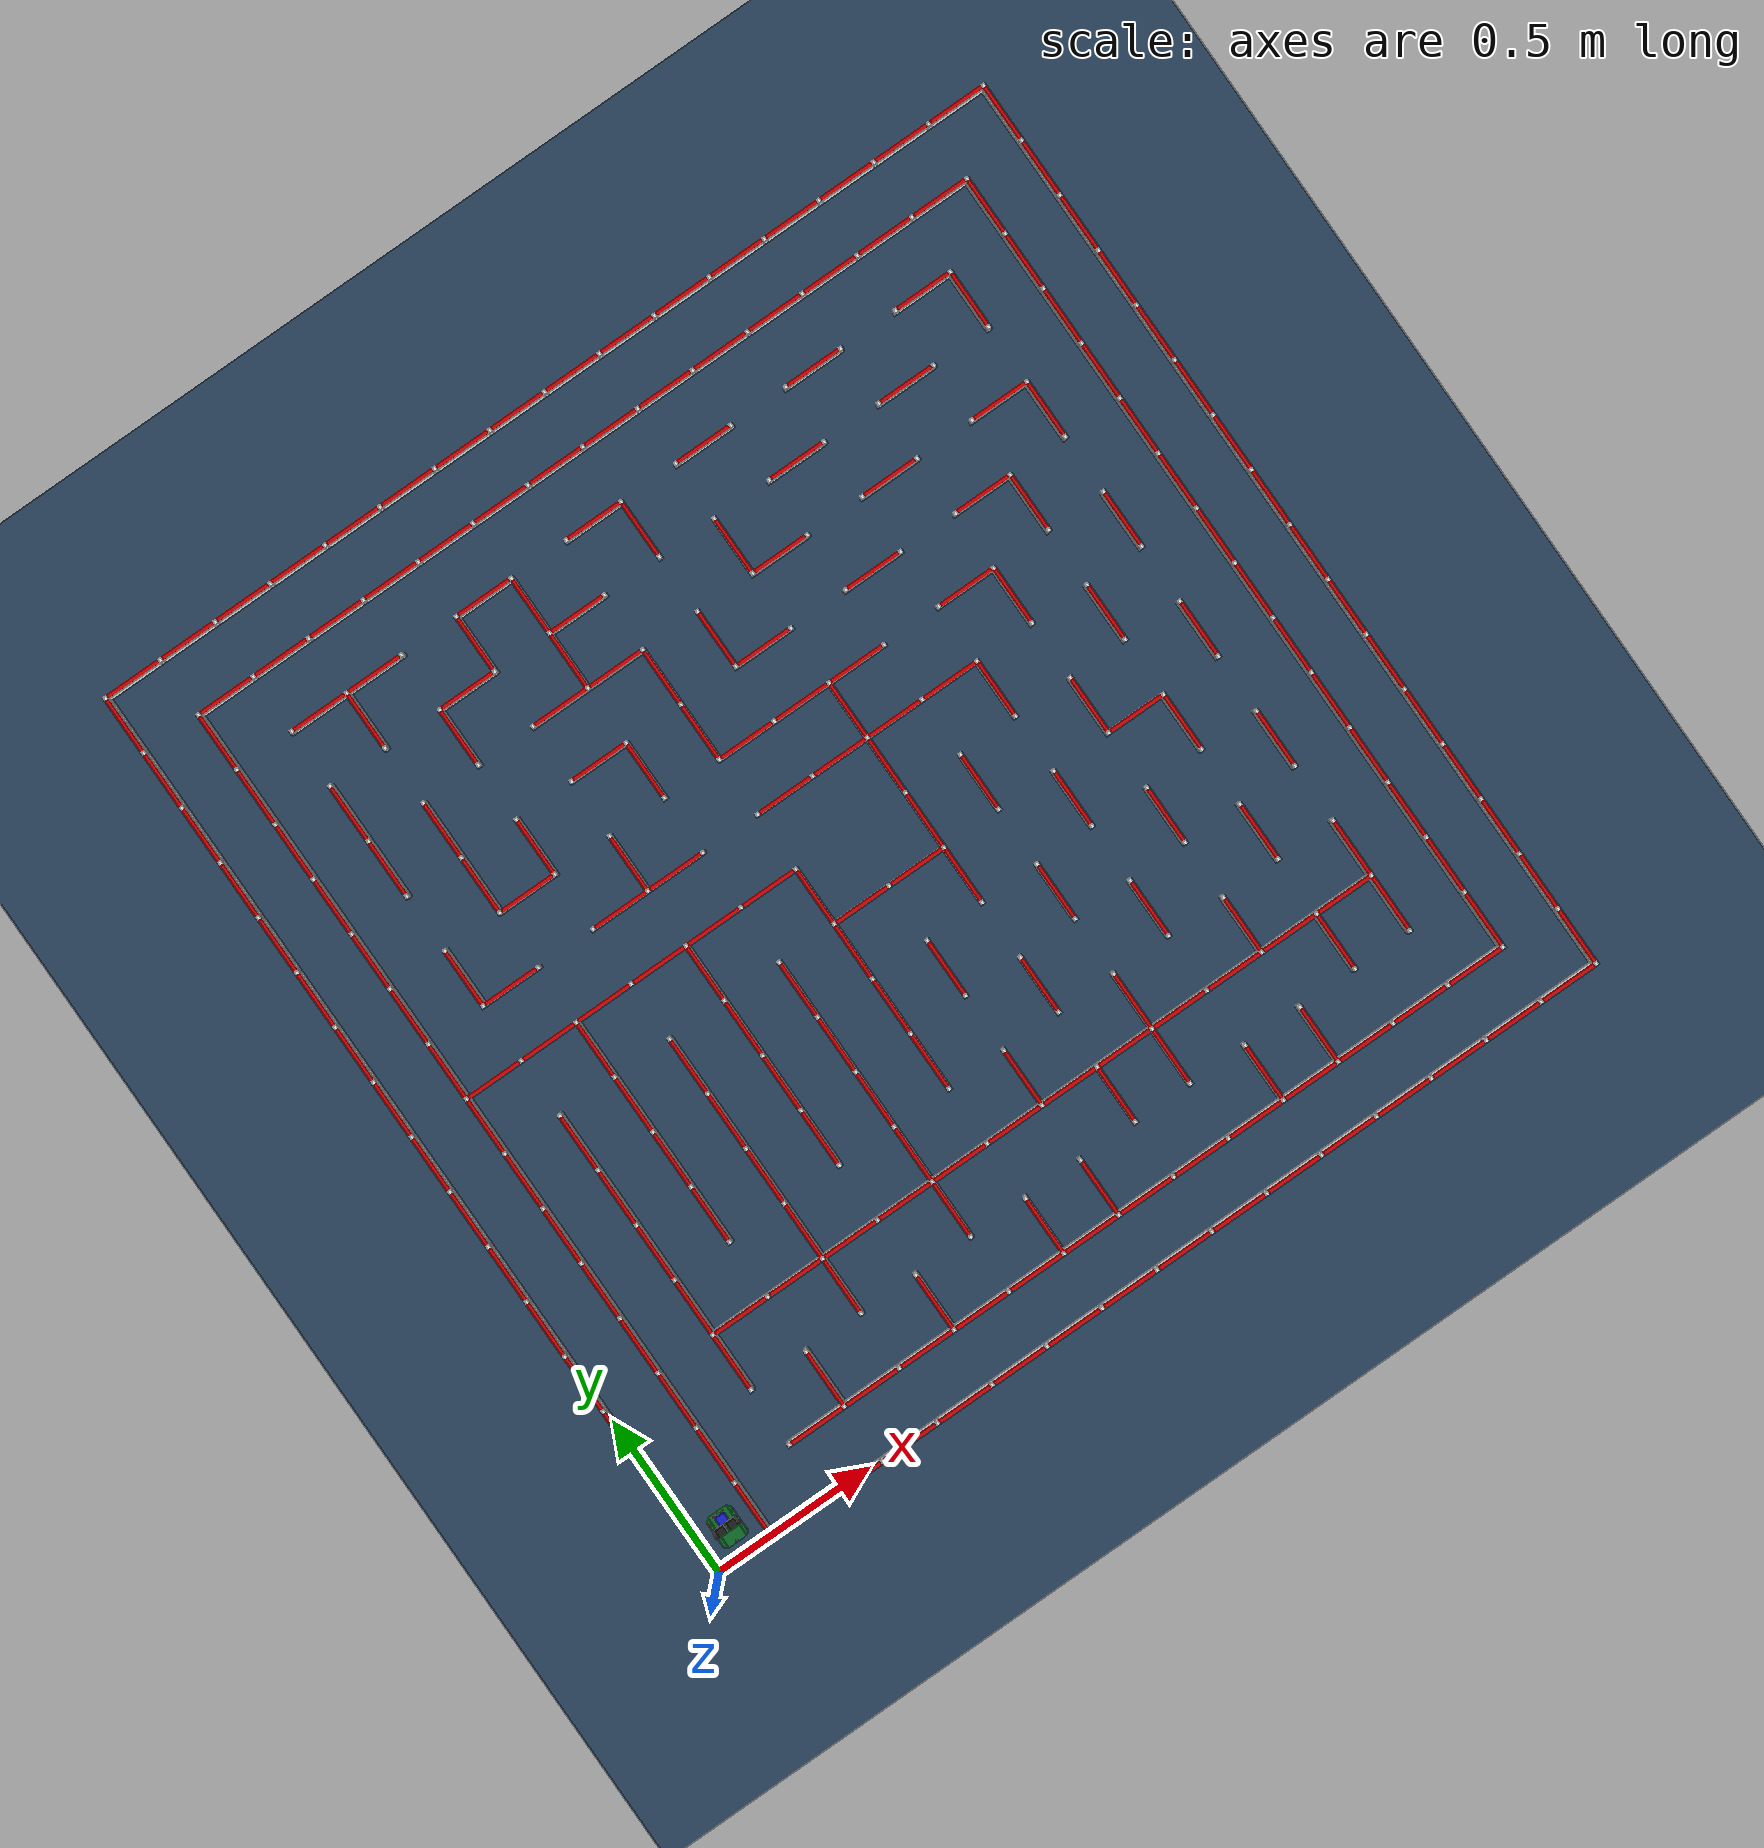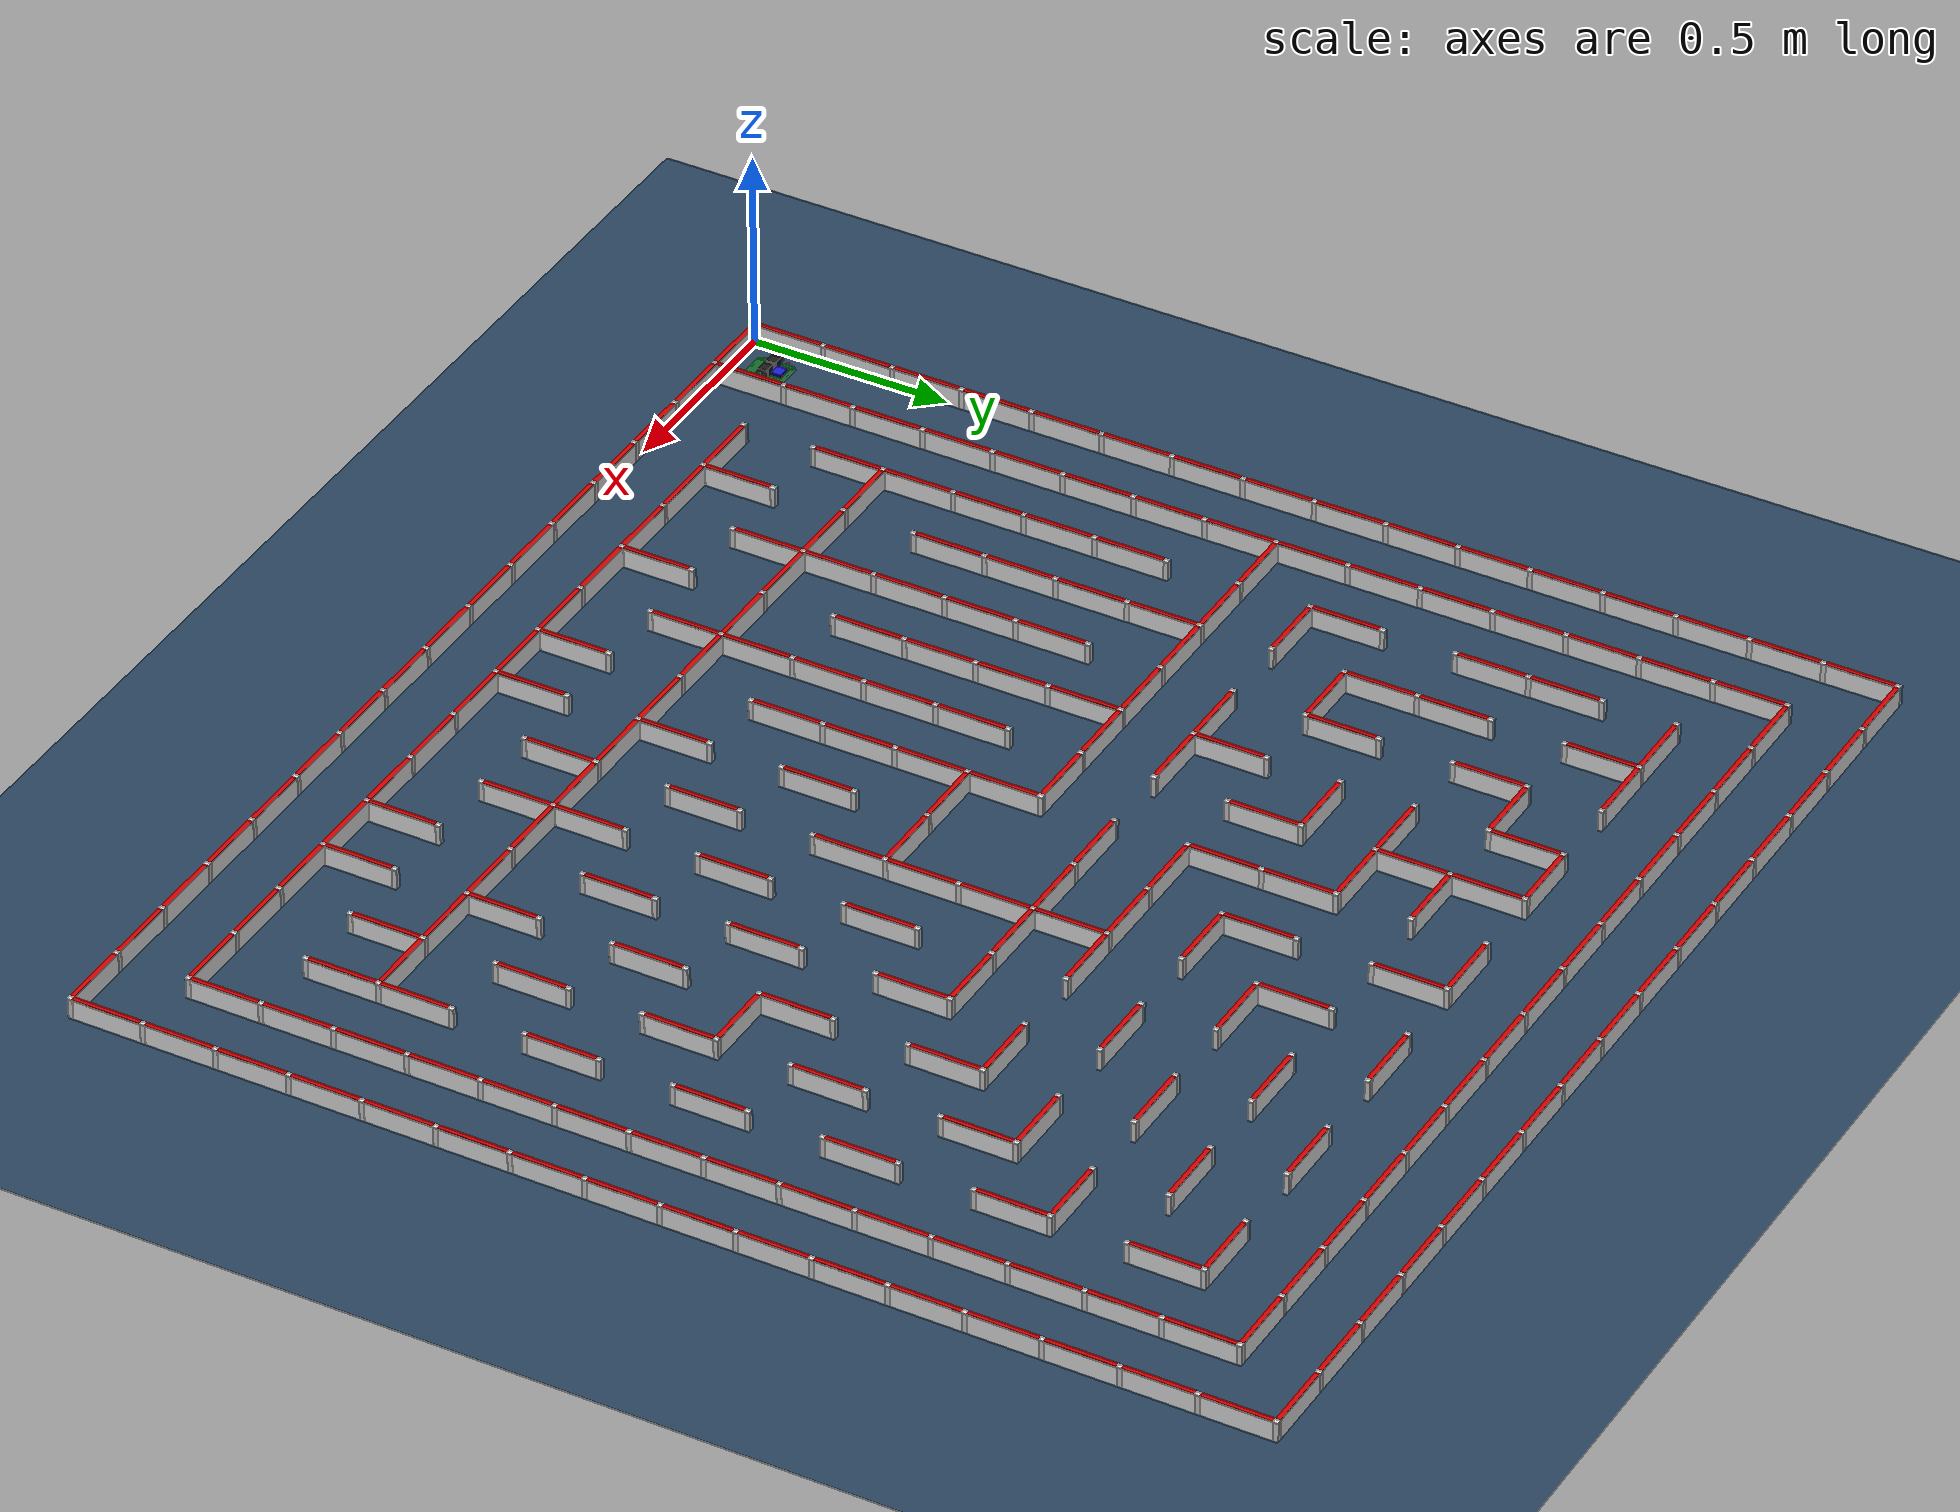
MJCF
<?xml version="1.0" ?>
<mujoco model="maze_16MM2017C_Chubu">
  <compiler angle="degree" coordinate="local" inertiafromgeom="true"/>
  <option timestep="0.0005" gravity="0 0 -9.81"/>
  <default>
    <geom solref="0.002 1"/>
  </default>
  <visual>
    <global offwidth="800" offheight="800"/>
  </visual>
  <asset>
    <texture name="tex_floor" type="2d" builtin="checker" rgb1=".2 .3 .4" rgb2=".1 .2 .3" width="512" height="512"/>
    <material name="mat_floor" texture="tex_floor" reflectance="0.0" texrepeat="11.11111111111111 11.11111111111111" texuniform="true"/>
    <material name="mat_wall" rgba="1 1 1 1"/>
    <material name="mat_wall_top" rgba="0.8 0 0 1"/>
    <material name="mat_post" rgba="0.9 0.9 0.9 1"/>
    <material name="mat_pcb" rgba="0.1 0.1 0.1 1" specular="0.5" shininess="0.5"/>
    <material name="mat_tire" rgba="0.1 0.1 0.1 1" reflectance="0.1"/>
    <material name="mat_wheel" rgba="0.9 0.9 0.9 1"/>
    <material name="mat_motor" rgba="0.6 0.6 0.6 1" specular="1" shininess="1"/>
    <material name="mat_battery" rgba="0.1 0.1 0.8 1"/>
    <material name="mat_sensor_body" rgba="0.2 0.2 0.2 1"/>
    <material name="mat_led" rgba="0.9 0.9 0.9 0.5"/>
    <mesh name="coner" vertex="0 0 -0.0008  0.036 0 -0.0008  0.026 0.01 -0.0008  0 0.01 -0.0008  0 0 0.0008  0.036 0 0.0008  0.026 0.01 0.0008  0 0.01 0.0008"/>
  </asset>
  <worldbody>
    <geom name="floor" type="plane" material="mat_floor" pos="1.44 1.44 0" size="2.0 2.0 0.1" friction="1.0 0.005 1e-4"/>
    <light diffuse=".5 .5 .5" pos="1.44 1.44 3" dir="0 0 -1"/>
    <geom name="post_0_0" type="box" size="0.006 0.006 0.025" pos="0.0 0.0 0.025" material="mat_post" friction="0.4 0.005 1e-4"/>
    <geom name="post_0_1" type="box" size="0.006 0.006 0.025" pos="0.0 0.18 0.025" material="mat_post" friction="0.4 0.005 1e-4"/>
    <geom name="post_0_2" type="box" size="0.006 0.006 0.025" pos="0.0 0.36 0.025" material="mat_post" friction="0.4 0.005 1e-4"/>
    <geom name="post_0_3" type="box" size="0.006 0.006 0.025" pos="0.0 0.54 0.025" material="mat_post" friction="0.4 0.005 1e-4"/>
    <geom name="post_0_4" type="box" size="0.006 0.006 0.025" pos="0.0 0.72 0.025" material="mat_post" friction="0.4 0.005 1e-4"/>
    <geom name="post_0_5" type="box" size="0.006 0.006 0.025" pos="0.0 0.8999999999999999 0.025" material="mat_post" friction="0.4 0.005 1e-4"/>
    <geom name="post_0_6" type="box" size="0.006 0.006 0.025" pos="0.0 1.08 0.025" material="mat_post" friction="0.4 0.005 1e-4"/>
    <geom name="post_0_7" type="box" size="0.006 0.006 0.025" pos="0.0 1.26 0.025" material="mat_post" friction="0.4 0.005 1e-4"/>
    <geom name="post_0_8" type="box" size="0.006 0.006 0.025" pos="0.0 1.44 0.025" material="mat_post" friction="0.4 0.005 1e-4"/>
    <geom name="post_0_9" type="box" size="0.006 0.006 0.025" pos="0.0 1.6199999999999999 0.025" material="mat_post" friction="0.4 0.005 1e-4"/>
    <geom name="post_0_10" type="box" size="0.006 0.006 0.025" pos="0.0 1.7999999999999998 0.025" material="mat_post" friction="0.4 0.005 1e-4"/>
    <geom name="post_0_11" type="box" size="0.006 0.006 0.025" pos="0.0 1.98 0.025" material="mat_post" friction="0.4 0.005 1e-4"/>
    <geom name="post_0_12" type="box" size="0.006 0.006 0.025" pos="0.0 2.16 0.025" material="mat_post" friction="0.4 0.005 1e-4"/>
    <geom name="post_0_13" type="box" size="0.006 0.006 0.025" pos="0.0 2.34 0.025" material="mat_post" friction="0.4 0.005 1e-4"/>
    <geom name="post_0_14" type="box" size="0.006 0.006 0.025" pos="0.0 2.52 0.025" material="mat_post" friction="0.4 0.005 1e-4"/>
    <geom name="post_0_15" type="box" size="0.006 0.006 0.025" pos="0.0 2.6999999999999997 0.025" material="mat_post" friction="0.4 0.005 1e-4"/>
    <geom name="post_0_16" type="box" size="0.006 0.006 0.025" pos="0.0 2.88 0.025" material="mat_post" friction="0.4 0.005 1e-4"/>
    <geom name="post_1_0" type="box" size="0.006 0.006 0.025" pos="0.18 0.0 0.025" material="mat_post" friction="0.4 0.005 1e-4"/>
    <geom name="post_1_1" type="box" size="0.006 0.006 0.025" pos="0.18 0.18 0.025" material="mat_post" friction="0.4 0.005 1e-4"/>
    <geom name="post_1_2" type="box" size="0.006 0.006 0.025" pos="0.18 0.36 0.025" material="mat_post" friction="0.4 0.005 1e-4"/>
    <geom name="post_1_3" type="box" size="0.006 0.006 0.025" pos="0.18 0.54 0.025" material="mat_post" friction="0.4 0.005 1e-4"/>
    <geom name="post_1_4" type="box" size="0.006 0.006 0.025" pos="0.18 0.72 0.025" material="mat_post" friction="0.4 0.005 1e-4"/>
    <geom name="post_1_5" type="box" size="0.006 0.006 0.025" pos="0.18 0.8999999999999999 0.025" material="mat_post" friction="0.4 0.005 1e-4"/>
    <geom name="post_1_6" type="box" size="0.006 0.006 0.025" pos="0.18 1.08 0.025" material="mat_post" friction="0.4 0.005 1e-4"/>
    <geom name="post_1_7" type="box" size="0.006 0.006 0.025" pos="0.18 1.26 0.025" material="mat_post" friction="0.4 0.005 1e-4"/>
    <geom name="post_1_8" type="box" size="0.006 0.006 0.025" pos="0.18 1.44 0.025" material="mat_post" friction="0.4 0.005 1e-4"/>
    <geom name="post_1_9" type="box" size="0.006 0.006 0.025" pos="0.18 1.6199999999999999 0.025" material="mat_post" friction="0.4 0.005 1e-4"/>
    <geom name="post_1_10" type="box" size="0.006 0.006 0.025" pos="0.18 1.7999999999999998 0.025" material="mat_post" friction="0.4 0.005 1e-4"/>
    <geom name="post_1_11" type="box" size="0.006 0.006 0.025" pos="0.18 1.98 0.025" material="mat_post" friction="0.4 0.005 1e-4"/>
    <geom name="post_1_12" type="box" size="0.006 0.006 0.025" pos="0.18 2.16 0.025" material="mat_post" friction="0.4 0.005 1e-4"/>
    <geom name="post_1_13" type="box" size="0.006 0.006 0.025" pos="0.18 2.34 0.025" material="mat_post" friction="0.4 0.005 1e-4"/>
    <geom name="post_1_14" type="box" size="0.006 0.006 0.025" pos="0.18 2.52 0.025" material="mat_post" friction="0.4 0.005 1e-4"/>
    <geom name="post_1_15" type="box" size="0.006 0.006 0.025" pos="0.18 2.6999999999999997 0.025" material="mat_post" friction="0.4 0.005 1e-4"/>
    <geom name="post_1_16" type="box" size="0.006 0.006 0.025" pos="0.18 2.88 0.025" material="mat_post" friction="0.4 0.005 1e-4"/>
    <geom name="post_2_0" type="box" size="0.006 0.006 0.025" pos="0.36 0.0 0.025" material="mat_post" friction="0.4 0.005 1e-4"/>
    <geom name="post_2_1" type="box" size="0.006 0.006 0.025" pos="0.36 0.18 0.025" material="mat_post" friction="0.4 0.005 1e-4"/>
    <geom name="post_2_2" type="box" size="0.006 0.006 0.025" pos="0.36 0.36 0.025" material="mat_post" friction="0.4 0.005 1e-4"/>
    <geom name="post_2_3" type="box" size="0.006 0.006 0.025" pos="0.36 0.54 0.025" material="mat_post" friction="0.4 0.005 1e-4"/>
    <geom name="post_2_4" type="box" size="0.006 0.006 0.025" pos="0.36 0.72 0.025" material="mat_post" friction="0.4 0.005 1e-4"/>
    <geom name="post_2_5" type="box" size="0.006 0.006 0.025" pos="0.36 0.8999999999999999 0.025" material="mat_post" friction="0.4 0.005 1e-4"/>
    <geom name="post_2_6" type="box" size="0.006 0.006 0.025" pos="0.36 1.08 0.025" material="mat_post" friction="0.4 0.005 1e-4"/>
    <geom name="post_2_7" type="box" size="0.006 0.006 0.025" pos="0.36 1.26 0.025" material="mat_post" friction="0.4 0.005 1e-4"/>
    <geom name="post_2_8" type="box" size="0.006 0.006 0.025" pos="0.36 1.44 0.025" material="mat_post" friction="0.4 0.005 1e-4"/>
    <geom name="post_2_9" type="box" size="0.006 0.006 0.025" pos="0.36 1.6199999999999999 0.025" material="mat_post" friction="0.4 0.005 1e-4"/>
    <geom name="post_2_10" type="box" size="0.006 0.006 0.025" pos="0.36 1.7999999999999998 0.025" material="mat_post" friction="0.4 0.005 1e-4"/>
    <geom name="post_2_11" type="box" size="0.006 0.006 0.025" pos="0.36 1.98 0.025" material="mat_post" friction="0.4 0.005 1e-4"/>
    <geom name="post_2_12" type="box" size="0.006 0.006 0.025" pos="0.36 2.16 0.025" material="mat_post" friction="0.4 0.005 1e-4"/>
    <geom name="post_2_13" type="box" size="0.006 0.006 0.025" pos="0.36 2.34 0.025" material="mat_post" friction="0.4 0.005 1e-4"/>
    <geom name="post_2_14" type="box" size="0.006 0.006 0.025" pos="0.36 2.52 0.025" material="mat_post" friction="0.4 0.005 1e-4"/>
    <geom name="post_2_15" type="box" size="0.006 0.006 0.025" pos="0.36 2.6999999999999997 0.025" material="mat_post" friction="0.4 0.005 1e-4"/>
    <geom name="post_2_16" type="box" size="0.006 0.006 0.025" pos="0.36 2.88 0.025" material="mat_post" friction="0.4 0.005 1e-4"/>
    <geom name="post_3_0" type="box" size="0.006 0.006 0.025" pos="0.54 0.0 0.025" material="mat_post" friction="0.4 0.005 1e-4"/>
    <geom name="post_3_1" type="box" size="0.006 0.006 0.025" pos="0.54 0.18 0.025" material="mat_post" friction="0.4 0.005 1e-4"/>
    <geom name="post_3_2" type="box" size="0.006 0.006 0.025" pos="0.54 0.36 0.025" material="mat_post" friction="0.4 0.005 1e-4"/>
    <geom name="post_3_3" type="box" size="0.006 0.006 0.025" pos="0.54 0.54 0.025" material="mat_post" friction="0.4 0.005 1e-4"/>
    <geom name="post_3_4" type="box" size="0.006 0.006 0.025" pos="0.54 0.72 0.025" material="mat_post" friction="0.4 0.005 1e-4"/>
    <geom name="post_3_5" type="box" size="0.006 0.006 0.025" pos="0.54 0.8999999999999999 0.025" material="mat_post" friction="0.4 0.005 1e-4"/>
    <geom name="post_3_6" type="box" size="0.006 0.006 0.025" pos="0.54 1.08 0.025" material="mat_post" friction="0.4 0.005 1e-4"/>
    <geom name="post_3_7" type="box" size="0.006 0.006 0.025" pos="0.54 1.26 0.025" material="mat_post" friction="0.4 0.005 1e-4"/>
    <geom name="post_3_8" type="box" size="0.006 0.006 0.025" pos="0.54 1.44 0.025" material="mat_post" friction="0.4 0.005 1e-4"/>
    <geom name="post_3_9" type="box" size="0.006 0.006 0.025" pos="0.54 1.6199999999999999 0.025" material="mat_post" friction="0.4 0.005 1e-4"/>
    <geom name="post_3_10" type="box" size="0.006 0.006 0.025" pos="0.54 1.7999999999999998 0.025" material="mat_post" friction="0.4 0.005 1e-4"/>
    <geom name="post_3_11" type="box" size="0.006 0.006 0.025" pos="0.54 1.98 0.025" material="mat_post" friction="0.4 0.005 1e-4"/>
    <geom name="post_3_12" type="box" size="0.006 0.006 0.025" pos="0.54 2.16 0.025" material="mat_post" friction="0.4 0.005 1e-4"/>
    <geom name="post_3_13" type="box" size="0.006 0.006 0.025" pos="0.54 2.34 0.025" material="mat_post" friction="0.4 0.005 1e-4"/>
    <geom name="post_3_14" type="box" size="0.006 0.006 0.025" pos="0.54 2.52 0.025" material="mat_post" friction="0.4 0.005 1e-4"/>
    <geom name="post_3_15" type="box" size="0.006 0.006 0.025" pos="0.54 2.6999999999999997 0.025" material="mat_post" friction="0.4 0.005 1e-4"/>
    <geom name="post_3_16" type="box" size="0.006 0.006 0.025" pos="0.54 2.88 0.025" material="mat_post" friction="0.4 0.005 1e-4"/>
    <geom name="post_4_0" type="box" size="0.006 0.006 0.025" pos="0.72 0.0 0.025" material="mat_post" friction="0.4 0.005 1e-4"/>
    <geom name="post_4_1" type="box" size="0.006 0.006 0.025" pos="0.72 0.18 0.025" material="mat_post" friction="0.4 0.005 1e-4"/>
    <geom name="post_4_2" type="box" size="0.006 0.006 0.025" pos="0.72 0.36 0.025" material="mat_post" friction="0.4 0.005 1e-4"/>
    <geom name="post_4_3" type="box" size="0.006 0.006 0.025" pos="0.72 0.54 0.025" material="mat_post" friction="0.4 0.005 1e-4"/>
    <geom name="post_4_4" type="box" size="0.006 0.006 0.025" pos="0.72 0.72 0.025" material="mat_post" friction="0.4 0.005 1e-4"/>
    <geom name="post_4_5" type="box" size="0.006 0.006 0.025" pos="0.72 0.8999999999999999 0.025" material="mat_post" friction="0.4 0.005 1e-4"/>
    <geom name="post_4_6" type="box" size="0.006 0.006 0.025" pos="0.72 1.08 0.025" material="mat_post" friction="0.4 0.005 1e-4"/>
    <geom name="post_4_7" type="box" size="0.006 0.006 0.025" pos="0.72 1.26 0.025" material="mat_post" friction="0.4 0.005 1e-4"/>
    <geom name="post_4_8" type="box" size="0.006 0.006 0.025" pos="0.72 1.44 0.025" material="mat_post" friction="0.4 0.005 1e-4"/>
    <geom name="post_4_9" type="box" size="0.006 0.006 0.025" pos="0.72 1.6199999999999999 0.025" material="mat_post" friction="0.4 0.005 1e-4"/>
    <geom name="post_4_10" type="box" size="0.006 0.006 0.025" pos="0.72 1.7999999999999998 0.025" material="mat_post" friction="0.4 0.005 1e-4"/>
    <geom name="post_4_11" type="box" size="0.006 0.006 0.025" pos="0.72 1.98 0.025" material="mat_post" friction="0.4 0.005 1e-4"/>
    <geom name="post_4_12" type="box" size="0.006 0.006 0.025" pos="0.72 2.16 0.025" material="mat_post" friction="0.4 0.005 1e-4"/>
    <geom name="post_4_13" type="box" size="0.006 0.006 0.025" pos="0.72 2.34 0.025" material="mat_post" friction="0.4 0.005 1e-4"/>
    <geom name="post_4_14" type="box" size="0.006 0.006 0.025" pos="0.72 2.52 0.025" material="mat_post" friction="0.4 0.005 1e-4"/>
    <geom name="post_4_15" type="box" size="0.006 0.006 0.025" pos="0.72 2.6999999999999997 0.025" material="mat_post" friction="0.4 0.005 1e-4"/>
    <geom name="post_4_16" type="box" size="0.006 0.006 0.025" pos="0.72 2.88 0.025" material="mat_post" friction="0.4 0.005 1e-4"/>
    <geom name="post_5_0" type="box" size="0.006 0.006 0.025" pos="0.8999999999999999 0.0 0.025" material="mat_post" friction="0.4 0.005 1e-4"/>
    <geom name="post_5_1" type="box" size="0.006 0.006 0.025" pos="0.8999999999999999 0.18 0.025" material="mat_post" friction="0.4 0.005 1e-4"/>
    <geom name="post_5_2" type="box" size="0.006 0.006 0.025" pos="0.8999999999999999 0.36 0.025" material="mat_post" friction="0.4 0.005 1e-4"/>
    <geom name="post_5_3" type="box" size="0.006 0.006 0.025" pos="0.8999999999999999 0.54 0.025" material="mat_post" friction="0.4 0.005 1e-4"/>
    <geom name="post_5_4" type="box" size="0.006 0.006 0.025" pos="0.8999999999999999 0.72 0.025" material="mat_post" friction="0.4 0.005 1e-4"/>
    <geom name="post_5_5" type="box" size="0.006 0.006 0.025" pos="0.8999999999999999 0.8999999999999999 0.025" material="mat_post" friction="0.4 0.005 1e-4"/>
    <geom name="post_5_6" type="box" size="0.006 0.006 0.025" pos="0.8999999999999999 1.08 0.025" material="mat_post" friction="0.4 0.005 1e-4"/>
    <geom name="post_5_7" type="box" size="0.006 0.006 0.025" pos="0.8999999999999999 1.26 0.025" material="mat_post" friction="0.4 0.005 1e-4"/>
    <geom name="post_5_8" type="box" size="0.006 0.006 0.025" pos="0.8999999999999999 1.44 0.025" material="mat_post" friction="0.4 0.005 1e-4"/>
    <geom name="post_5_9" type="box" size="0.006 0.006 0.025" pos="0.8999999999999999 1.6199999999999999 0.025" material="mat_post" friction="0.4 0.005 1e-4"/>
    <geom name="post_5_10" type="box" size="0.006 0.006 0.025" pos="0.8999999999999999 1.7999999999999998 0.025" material="mat_post" friction="0.4 0.005 1e-4"/>
    <geom name="post_5_11" type="box" size="0.006 0.006 0.025" pos="0.8999999999999999 1.98 0.025" material="mat_post" friction="0.4 0.005 1e-4"/>
    <geom name="post_5_12" type="box" size="0.006 0.006 0.025" pos="0.8999999999999999 2.16 0.025" material="mat_post" friction="0.4 0.005 1e-4"/>
    <geom name="post_5_13" type="box" size="0.006 0.006 0.025" pos="0.8999999999999999 2.34 0.025" material="mat_post" friction="0.4 0.005 1e-4"/>
    <geom name="post_5_14" type="box" size="0.006 0.006 0.025" pos="0.8999999999999999 2.52 0.025" material="mat_post" friction="0.4 0.005 1e-4"/>
    <geom name="post_5_15" type="box" size="0.006 0.006 0.025" pos="0.8999999999999999 2.6999999999999997 0.025" material="mat_post" friction="0.4 0.005 1e-4"/>
    <geom name="post_5_16" type="box" size="0.006 0.006 0.025" pos="0.8999999999999999 2.88 0.025" material="mat_post" friction="0.4 0.005 1e-4"/>
    <geom name="post_6_0" type="box" size="0.006 0.006 0.025" pos="1.08 0.0 0.025" material="mat_post" friction="0.4 0.005 1e-4"/>
    <geom name="post_6_1" type="box" size="0.006 0.006 0.025" pos="1.08 0.18 0.025" material="mat_post" friction="0.4 0.005 1e-4"/>
    <geom name="post_6_2" type="box" size="0.006 0.006 0.025" pos="1.08 0.36 0.025" material="mat_post" friction="0.4 0.005 1e-4"/>
    <geom name="post_6_3" type="box" size="0.006 0.006 0.025" pos="1.08 0.54 0.025" material="mat_post" friction="0.4 0.005 1e-4"/>
    <geom name="post_6_4" type="box" size="0.006 0.006 0.025" pos="1.08 0.72 0.025" material="mat_post" friction="0.4 0.005 1e-4"/>
    <geom name="post_6_5" type="box" size="0.006 0.006 0.025" pos="1.08 0.8999999999999999 0.025" material="mat_post" friction="0.4 0.005 1e-4"/>
    <geom name="post_6_6" type="box" size="0.006 0.006 0.025" pos="1.08 1.08 0.025" material="mat_post" friction="0.4 0.005 1e-4"/>
    <geom name="post_6_7" type="box" size="0.006 0.006 0.025" pos="1.08 1.26 0.025" material="mat_post" friction="0.4 0.005 1e-4"/>
    <geom name="post_6_8" type="box" size="0.006 0.006 0.025" pos="1.08 1.44 0.025" material="mat_post" friction="0.4 0.005 1e-4"/>
    <geom name="post_6_9" type="box" size="0.006 0.006 0.025" pos="1.08 1.6199999999999999 0.025" material="mat_post" friction="0.4 0.005 1e-4"/>
    <geom name="post_6_10" type="box" size="0.006 0.006 0.025" pos="1.08 1.7999999999999998 0.025" material="mat_post" friction="0.4 0.005 1e-4"/>
    <geom name="post_6_11" type="box" size="0.006 0.006 0.025" pos="1.08 1.98 0.025" material="mat_post" friction="0.4 0.005 1e-4"/>
    <geom name="post_6_12" type="box" size="0.006 0.006 0.025" pos="1.08 2.16 0.025" material="mat_post" friction="0.4 0.005 1e-4"/>
    <geom name="post_6_13" type="box" size="0.006 0.006 0.025" pos="1.08 2.34 0.025" material="mat_post" friction="0.4 0.005 1e-4"/>
    <geom name="post_6_14" type="box" size="0.006 0.006 0.025" pos="1.08 2.52 0.025" material="mat_post" friction="0.4 0.005 1e-4"/>
    <geom name="post_6_15" type="box" size="0.006 0.006 0.025" pos="1.08 2.6999999999999997 0.025" material="mat_post" friction="0.4 0.005 1e-4"/>
    <geom name="post_6_16" type="box" size="0.006 0.006 0.025" pos="1.08 2.88 0.025" material="mat_post" friction="0.4 0.005 1e-4"/>
    <geom name="post_7_0" type="box" size="0.006 0.006 0.025" pos="1.26 0.0 0.025" material="mat_post" friction="0.4 0.005 1e-4"/>
    <geom name="post_7_1" type="box" size="0.006 0.006 0.025" pos="1.26 0.18 0.025" material="mat_post" friction="0.4 0.005 1e-4"/>
    <geom name="post_7_2" type="box" size="0.006 0.006 0.025" pos="1.26 0.36 0.025" material="mat_post" friction="0.4 0.005 1e-4"/>
    <geom name="post_7_3" type="box" size="0.006 0.006 0.025" pos="1.26 0.54 0.025" material="mat_post" friction="0.4 0.005 1e-4"/>
    <geom name="post_7_4" type="box" size="0.006 0.006 0.025" pos="1.26 0.72 0.025" material="mat_post" friction="0.4 0.005 1e-4"/>
    <geom name="post_7_5" type="box" size="0.006 0.006 0.025" pos="1.26 0.8999999999999999 0.025" material="mat_post" friction="0.4 0.005 1e-4"/>
    <geom name="post_7_6" type="box" size="0.006 0.006 0.025" pos="1.26 1.08 0.025" material="mat_post" friction="0.4 0.005 1e-4"/>
    <geom name="post_7_7" type="box" size="0.006 0.006 0.025" pos="1.26 1.26 0.025" material="mat_post" friction="0.4 0.005 1e-4"/>
    <geom name="post_7_8" type="box" size="0.006 0.006 0.025" pos="1.26 1.44 0.025" material="mat_post" friction="0.4 0.005 1e-4"/>
    <geom name="post_7_9" type="box" size="0.006 0.006 0.025" pos="1.26 1.6199999999999999 0.025" material="mat_post" friction="0.4 0.005 1e-4"/>
    <geom name="post_7_10" type="box" size="0.006 0.006 0.025" pos="1.26 1.7999999999999998 0.025" material="mat_post" friction="0.4 0.005 1e-4"/>
    <geom name="post_7_11" type="box" size="0.006 0.006 0.025" pos="1.26 1.98 0.025" material="mat_post" friction="0.4 0.005 1e-4"/>
    <geom name="post_7_12" type="box" size="0.006 0.006 0.025" pos="1.26 2.16 0.025" material="mat_post" friction="0.4 0.005 1e-4"/>
    <geom name="post_7_13" type="box" size="0.006 0.006 0.025" pos="1.26 2.34 0.025" material="mat_post" friction="0.4 0.005 1e-4"/>
    <geom name="post_7_14" type="box" size="0.006 0.006 0.025" pos="1.26 2.52 0.025" material="mat_post" friction="0.4 0.005 1e-4"/>
    <geom name="post_7_15" type="box" size="0.006 0.006 0.025" pos="1.26 2.6999999999999997 0.025" material="mat_post" friction="0.4 0.005 1e-4"/>
    <geom name="post_7_16" type="box" size="0.006 0.006 0.025" pos="1.26 2.88 0.025" material="mat_post" friction="0.4 0.005 1e-4"/>
    <geom name="post_8_0" type="box" size="0.006 0.006 0.025" pos="1.44 0.0 0.025" material="mat_post" friction="0.4 0.005 1e-4"/>
    <geom name="post_8_1" type="box" size="0.006 0.006 0.025" pos="1.44 0.18 0.025" material="mat_post" friction="0.4 0.005 1e-4"/>
    <geom name="post_8_2" type="box" size="0.006 0.006 0.025" pos="1.44 0.36 0.025" material="mat_post" friction="0.4 0.005 1e-4"/>
    <geom name="post_8_3" type="box" size="0.006 0.006 0.025" pos="1.44 0.54 0.025" material="mat_post" friction="0.4 0.005 1e-4"/>
    <geom name="post_8_4" type="box" size="0.006 0.006 0.025" pos="1.44 0.72 0.025" material="mat_post" friction="0.4 0.005 1e-4"/>
    <geom name="post_8_5" type="box" size="0.006 0.006 0.025" pos="1.44 0.8999999999999999 0.025" material="mat_post" friction="0.4 0.005 1e-4"/>
    <geom name="post_8_6" type="box" size="0.006 0.006 0.025" pos="1.44 1.08 0.025" material="mat_post" friction="0.4 0.005 1e-4"/>
    <geom name="post_8_7" type="box" size="0.006 0.006 0.025" pos="1.44 1.26 0.025" material="mat_post" friction="0.4 0.005 1e-4"/>
    <geom name="post_8_9" type="box" size="0.006 0.006 0.025" pos="1.44 1.6199999999999999 0.025" material="mat_post" friction="0.4 0.005 1e-4"/>
    <geom name="post_8_10" type="box" size="0.006 0.006 0.025" pos="1.44 1.7999999999999998 0.025" material="mat_post" friction="0.4 0.005 1e-4"/>
    <geom name="post_8_11" type="box" size="0.006 0.006 0.025" pos="1.44 1.98 0.025" material="mat_post" friction="0.4 0.005 1e-4"/>
    <geom name="post_8_12" type="box" size="0.006 0.006 0.025" pos="1.44 2.16 0.025" material="mat_post" friction="0.4 0.005 1e-4"/>
    <geom name="post_8_13" type="box" size="0.006 0.006 0.025" pos="1.44 2.34 0.025" material="mat_post" friction="0.4 0.005 1e-4"/>
    <geom name="post_8_14" type="box" size="0.006 0.006 0.025" pos="1.44 2.52 0.025" material="mat_post" friction="0.4 0.005 1e-4"/>
    <geom name="post_8_15" type="box" size="0.006 0.006 0.025" pos="1.44 2.6999999999999997 0.025" material="mat_post" friction="0.4 0.005 1e-4"/>
    <geom name="post_8_16" type="box" size="0.006 0.006 0.025" pos="1.44 2.88 0.025" material="mat_post" friction="0.4 0.005 1e-4"/>
    <geom name="post_9_0" type="box" size="0.006 0.006 0.025" pos="1.6199999999999999 0.0 0.025" material="mat_post" friction="0.4 0.005 1e-4"/>
    <geom name="post_9_1" type="box" size="0.006 0.006 0.025" pos="1.6199999999999999 0.18 0.025" material="mat_post" friction="0.4 0.005 1e-4"/>
    <geom name="post_9_2" type="box" size="0.006 0.006 0.025" pos="1.6199999999999999 0.36 0.025" material="mat_post" friction="0.4 0.005 1e-4"/>
    <geom name="post_9_3" type="box" size="0.006 0.006 0.025" pos="1.6199999999999999 0.54 0.025" material="mat_post" friction="0.4 0.005 1e-4"/>
    <geom name="post_9_4" type="box" size="0.006 0.006 0.025" pos="1.6199999999999999 0.72 0.025" material="mat_post" friction="0.4 0.005 1e-4"/>
    <geom name="post_9_5" type="box" size="0.006 0.006 0.025" pos="1.6199999999999999 0.8999999999999999 0.025" material="mat_post" friction="0.4 0.005 1e-4"/>
    <geom name="post_9_6" type="box" size="0.006 0.006 0.025" pos="1.6199999999999999 1.08 0.025" material="mat_post" friction="0.4 0.005 1e-4"/>
    <geom name="post_9_7" type="box" size="0.006 0.006 0.025" pos="1.6199999999999999 1.26 0.025" material="mat_post" friction="0.4 0.005 1e-4"/>
    <geom name="post_9_8" type="box" size="0.006 0.006 0.025" pos="1.6199999999999999 1.44 0.025" material="mat_post" friction="0.4 0.005 1e-4"/>
    <geom name="post_9_9" type="box" size="0.006 0.006 0.025" pos="1.6199999999999999 1.6199999999999999 0.025" material="mat_post" friction="0.4 0.005 1e-4"/>
    <geom name="post_9_10" type="box" size="0.006 0.006 0.025" pos="1.6199999999999999 1.7999999999999998 0.025" material="mat_post" friction="0.4 0.005 1e-4"/>
    <geom name="post_9_11" type="box" size="0.006 0.006 0.025" pos="1.6199999999999999 1.98 0.025" material="mat_post" friction="0.4 0.005 1e-4"/>
    <geom name="post_9_12" type="box" size="0.006 0.006 0.025" pos="1.6199999999999999 2.16 0.025" material="mat_post" friction="0.4 0.005 1e-4"/>
    <geom name="post_9_13" type="box" size="0.006 0.006 0.025" pos="1.6199999999999999 2.34 0.025" material="mat_post" friction="0.4 0.005 1e-4"/>
    <geom name="post_9_14" type="box" size="0.006 0.006 0.025" pos="1.6199999999999999 2.52 0.025" material="mat_post" friction="0.4 0.005 1e-4"/>
    <geom name="post_9_15" type="box" size="0.006 0.006 0.025" pos="1.6199999999999999 2.6999999999999997 0.025" material="mat_post" friction="0.4 0.005 1e-4"/>
    <geom name="post_9_16" type="box" size="0.006 0.006 0.025" pos="1.6199999999999999 2.88 0.025" material="mat_post" friction="0.4 0.005 1e-4"/>
    <geom name="post_10_0" type="box" size="0.006 0.006 0.025" pos="1.7999999999999998 0.0 0.025" material="mat_post" friction="0.4 0.005 1e-4"/>
    <geom name="post_10_1" type="box" size="0.006 0.006 0.025" pos="1.7999999999999998 0.18 0.025" material="mat_post" friction="0.4 0.005 1e-4"/>
    <geom name="post_10_2" type="box" size="0.006 0.006 0.025" pos="1.7999999999999998 0.36 0.025" material="mat_post" friction="0.4 0.005 1e-4"/>
    <geom name="post_10_3" type="box" size="0.006 0.006 0.025" pos="1.7999999999999998 0.54 0.025" material="mat_post" friction="0.4 0.005 1e-4"/>
    <geom name="post_10_4" type="box" size="0.006 0.006 0.025" pos="1.7999999999999998 0.72 0.025" material="mat_post" friction="0.4 0.005 1e-4"/>
    <geom name="post_10_5" type="box" size="0.006 0.006 0.025" pos="1.7999999999999998 0.8999999999999999 0.025" material="mat_post" friction="0.4 0.005 1e-4"/>
    <geom name="post_10_6" type="box" size="0.006 0.006 0.025" pos="1.7999999999999998 1.08 0.025" material="mat_post" friction="0.4 0.005 1e-4"/>
    <geom name="post_10_7" type="box" size="0.006 0.006 0.025" pos="1.7999999999999998 1.26 0.025" material="mat_post" friction="0.4 0.005 1e-4"/>
    <geom name="post_10_8" type="box" size="0.006 0.006 0.025" pos="1.7999999999999998 1.44 0.025" material="mat_post" friction="0.4 0.005 1e-4"/>
    <geom name="post_10_9" type="box" size="0.006 0.006 0.025" pos="1.7999999999999998 1.6199999999999999 0.025" material="mat_post" friction="0.4 0.005 1e-4"/>
    <geom name="post_10_10" type="box" size="0.006 0.006 0.025" pos="1.7999999999999998 1.7999999999999998 0.025" material="mat_post" friction="0.4 0.005 1e-4"/>
    <geom name="post_10_11" type="box" size="0.006 0.006 0.025" pos="1.7999999999999998 1.98 0.025" material="mat_post" friction="0.4 0.005 1e-4"/>
    <geom name="post_10_12" type="box" size="0.006 0.006 0.025" pos="1.7999999999999998 2.16 0.025" material="mat_post" friction="0.4 0.005 1e-4"/>
    <geom name="post_10_13" type="box" size="0.006 0.006 0.025" pos="1.7999999999999998 2.34 0.025" material="mat_post" friction="0.4 0.005 1e-4"/>
    <geom name="post_10_14" type="box" size="0.006 0.006 0.025" pos="1.7999999999999998 2.52 0.025" material="mat_post" friction="0.4 0.005 1e-4"/>
    <geom name="post_10_15" type="box" size="0.006 0.006 0.025" pos="1.7999999999999998 2.6999999999999997 0.025" material="mat_post" friction="0.4 0.005 1e-4"/>
    <geom name="post_10_16" type="box" size="0.006 0.006 0.025" pos="1.7999999999999998 2.88 0.025" material="mat_post" friction="0.4 0.005 1e-4"/>
    <geom name="post_11_0" type="box" size="0.006 0.006 0.025" pos="1.98 0.0 0.025" material="mat_post" friction="0.4 0.005 1e-4"/>
    <geom name="post_11_1" type="box" size="0.006 0.006 0.025" pos="1.98 0.18 0.025" material="mat_post" friction="0.4 0.005 1e-4"/>
    <geom name="post_11_2" type="box" size="0.006 0.006 0.025" pos="1.98 0.36 0.025" material="mat_post" friction="0.4 0.005 1e-4"/>
    <geom name="post_11_3" type="box" size="0.006 0.006 0.025" pos="1.98 0.54 0.025" material="mat_post" friction="0.4 0.005 1e-4"/>
    <geom name="post_11_4" type="box" size="0.006 0.006 0.025" pos="1.98 0.72 0.025" material="mat_post" friction="0.4 0.005 1e-4"/>
    <geom name="post_11_5" type="box" size="0.006 0.006 0.025" pos="1.98 0.8999999999999999 0.025" material="mat_post" friction="0.4 0.005 1e-4"/>
    <geom name="post_11_6" type="box" size="0.006 0.006 0.025" pos="1.98 1.08 0.025" material="mat_post" friction="0.4 0.005 1e-4"/>
    <geom name="post_11_7" type="box" size="0.006 0.006 0.025" pos="1.98 1.26 0.025" material="mat_post" friction="0.4 0.005 1e-4"/>
    <geom name="post_11_8" type="box" size="0.006 0.006 0.025" pos="1.98 1.44 0.025" material="mat_post" friction="0.4 0.005 1e-4"/>
    <geom name="post_11_9" type="box" size="0.006 0.006 0.025" pos="1.98 1.6199999999999999 0.025" material="mat_post" friction="0.4 0.005 1e-4"/>
    <geom name="post_11_10" type="box" size="0.006 0.006 0.025" pos="1.98 1.7999999999999998 0.025" material="mat_post" friction="0.4 0.005 1e-4"/>
    <geom name="post_11_11" type="box" size="0.006 0.006 0.025" pos="1.98 1.98 0.025" material="mat_post" friction="0.4 0.005 1e-4"/>
    <geom name="post_11_12" type="box" size="0.006 0.006 0.025" pos="1.98 2.16 0.025" material="mat_post" friction="0.4 0.005 1e-4"/>
    <geom name="post_11_13" type="box" size="0.006 0.006 0.025" pos="1.98 2.34 0.025" material="mat_post" friction="0.4 0.005 1e-4"/>
    <geom name="post_11_14" type="box" size="0.006 0.006 0.025" pos="1.98 2.52 0.025" material="mat_post" friction="0.4 0.005 1e-4"/>
    <geom name="post_11_15" type="box" size="0.006 0.006 0.025" pos="1.98 2.6999999999999997 0.025" material="mat_post" friction="0.4 0.005 1e-4"/>
    <geom name="post_11_16" type="box" size="0.006 0.006 0.025" pos="1.98 2.88 0.025" material="mat_post" friction="0.4 0.005 1e-4"/>
    <geom name="post_12_0" type="box" size="0.006 0.006 0.025" pos="2.16 0.0 0.025" material="mat_post" friction="0.4 0.005 1e-4"/>
    <geom name="post_12_1" type="box" size="0.006 0.006 0.025" pos="2.16 0.18 0.025" material="mat_post" friction="0.4 0.005 1e-4"/>
    <geom name="post_12_2" type="box" size="0.006 0.006 0.025" pos="2.16 0.36 0.025" material="mat_post" friction="0.4 0.005 1e-4"/>
    <geom name="post_12_3" type="box" size="0.006 0.006 0.025" pos="2.16 0.54 0.025" material="mat_post" friction="0.4 0.005 1e-4"/>
    <geom name="post_12_4" type="box" size="0.006 0.006 0.025" pos="2.16 0.72 0.025" material="mat_post" friction="0.4 0.005 1e-4"/>
    <geom name="post_12_5" type="box" size="0.006 0.006 0.025" pos="2.16 0.8999999999999999 0.025" material="mat_post" friction="0.4 0.005 1e-4"/>
    <geom name="post_12_6" type="box" size="0.006 0.006 0.025" pos="2.16 1.08 0.025" material="mat_post" friction="0.4 0.005 1e-4"/>
    <geom name="post_12_7" type="box" size="0.006 0.006 0.025" pos="2.16 1.26 0.025" material="mat_post" friction="0.4 0.005 1e-4"/>
    <geom name="post_12_8" type="box" size="0.006 0.006 0.025" pos="2.16 1.44 0.025" material="mat_post" friction="0.4 0.005 1e-4"/>
    <geom name="post_12_9" type="box" size="0.006 0.006 0.025" pos="2.16 1.6199999999999999 0.025" material="mat_post" friction="0.4 0.005 1e-4"/>
    <geom name="post_12_10" type="box" size="0.006 0.006 0.025" pos="2.16 1.7999999999999998 0.025" material="mat_post" friction="0.4 0.005 1e-4"/>
    <geom name="post_12_11" type="box" size="0.006 0.006 0.025" pos="2.16 1.98 0.025" material="mat_post" friction="0.4 0.005 1e-4"/>
    <geom name="post_12_12" type="box" size="0.006 0.006 0.025" pos="2.16 2.16 0.025" material="mat_post" friction="0.4 0.005 1e-4"/>
    <geom name="post_12_13" type="box" size="0.006 0.006 0.025" pos="2.16 2.34 0.025" material="mat_post" friction="0.4 0.005 1e-4"/>
    <geom name="post_12_14" type="box" size="0.006 0.006 0.025" pos="2.16 2.52 0.025" material="mat_post" friction="0.4 0.005 1e-4"/>
    <geom name="post_12_15" type="box" size="0.006 0.006 0.025" pos="2.16 2.6999999999999997 0.025" material="mat_post" friction="0.4 0.005 1e-4"/>
    <geom name="post_12_16" type="box" size="0.006 0.006 0.025" pos="2.16 2.88 0.025" material="mat_post" friction="0.4 0.005 1e-4"/>
    <geom name="post_13_0" type="box" size="0.006 0.006 0.025" pos="2.34 0.0 0.025" material="mat_post" friction="0.4 0.005 1e-4"/>
    <geom name="post_13_1" type="box" size="0.006 0.006 0.025" pos="2.34 0.18 0.025" material="mat_post" friction="0.4 0.005 1e-4"/>
    <geom name="post_13_2" type="box" size="0.006 0.006 0.025" pos="2.34 0.36 0.025" material="mat_post" friction="0.4 0.005 1e-4"/>
    <geom name="post_13_3" type="box" size="0.006 0.006 0.025" pos="2.34 0.54 0.025" material="mat_post" friction="0.4 0.005 1e-4"/>
    <geom name="post_13_4" type="box" size="0.006 0.006 0.025" pos="2.34 0.72 0.025" material="mat_post" friction="0.4 0.005 1e-4"/>
    <geom name="post_13_5" type="box" size="0.006 0.006 0.025" pos="2.34 0.8999999999999999 0.025" material="mat_post" friction="0.4 0.005 1e-4"/>
    <geom name="post_13_6" type="box" size="0.006 0.006 0.025" pos="2.34 1.08 0.025" material="mat_post" friction="0.4 0.005 1e-4"/>
    <geom name="post_13_7" type="box" size="0.006 0.006 0.025" pos="2.34 1.26 0.025" material="mat_post" friction="0.4 0.005 1e-4"/>
    <geom name="post_13_8" type="box" size="0.006 0.006 0.025" pos="2.34 1.44 0.025" material="mat_post" friction="0.4 0.005 1e-4"/>
    <geom name="post_13_9" type="box" size="0.006 0.006 0.025" pos="2.34 1.6199999999999999 0.025" material="mat_post" friction="0.4 0.005 1e-4"/>
    <geom name="post_13_10" type="box" size="0.006 0.006 0.025" pos="2.34 1.7999999999999998 0.025" material="mat_post" friction="0.4 0.005 1e-4"/>
    <geom name="post_13_11" type="box" size="0.006 0.006 0.025" pos="2.34 1.98 0.025" material="mat_post" friction="0.4 0.005 1e-4"/>
    <geom name="post_13_12" type="box" size="0.006 0.006 0.025" pos="2.34 2.16 0.025" material="mat_post" friction="0.4 0.005 1e-4"/>
    <geom name="post_13_13" type="box" size="0.006 0.006 0.025" pos="2.34 2.34 0.025" material="mat_post" friction="0.4 0.005 1e-4"/>
    <geom name="post_13_14" type="box" size="0.006 0.006 0.025" pos="2.34 2.52 0.025" material="mat_post" friction="0.4 0.005 1e-4"/>
    <geom name="post_13_15" type="box" size="0.006 0.006 0.025" pos="2.34 2.6999999999999997 0.025" material="mat_post" friction="0.4 0.005 1e-4"/>
    <geom name="post_13_16" type="box" size="0.006 0.006 0.025" pos="2.34 2.88 0.025" material="mat_post" friction="0.4 0.005 1e-4"/>
    <geom name="post_14_0" type="box" size="0.006 0.006 0.025" pos="2.52 0.0 0.025" material="mat_post" friction="0.4 0.005 1e-4"/>
    <geom name="post_14_1" type="box" size="0.006 0.006 0.025" pos="2.52 0.18 0.025" material="mat_post" friction="0.4 0.005 1e-4"/>
    <geom name="post_14_2" type="box" size="0.006 0.006 0.025" pos="2.52 0.36 0.025" material="mat_post" friction="0.4 0.005 1e-4"/>
    <geom name="post_14_3" type="box" size="0.006 0.006 0.025" pos="2.52 0.54 0.025" material="mat_post" friction="0.4 0.005 1e-4"/>
    <geom name="post_14_4" type="box" size="0.006 0.006 0.025" pos="2.52 0.72 0.025" material="mat_post" friction="0.4 0.005 1e-4"/>
    <geom name="post_14_5" type="box" size="0.006 0.006 0.025" pos="2.52 0.8999999999999999 0.025" material="mat_post" friction="0.4 0.005 1e-4"/>
    <geom name="post_14_6" type="box" size="0.006 0.006 0.025" pos="2.52 1.08 0.025" material="mat_post" friction="0.4 0.005 1e-4"/>
    <geom name="post_14_7" type="box" size="0.006 0.006 0.025" pos="2.52 1.26 0.025" material="mat_post" friction="0.4 0.005 1e-4"/>
    <geom name="post_14_8" type="box" size="0.006 0.006 0.025" pos="2.52 1.44 0.025" material="mat_post" friction="0.4 0.005 1e-4"/>
    <geom name="post_14_9" type="box" size="0.006 0.006 0.025" pos="2.52 1.6199999999999999 0.025" material="mat_post" friction="0.4 0.005 1e-4"/>
    <geom name="post_14_10" type="box" size="0.006 0.006 0.025" pos="2.52 1.7999999999999998 0.025" material="mat_post" friction="0.4 0.005 1e-4"/>
    <geom name="post_14_11" type="box" size="0.006 0.006 0.025" pos="2.52 1.98 0.025" material="mat_post" friction="0.4 0.005 1e-4"/>
    <geom name="post_14_12" type="box" size="0.006 0.006 0.025" pos="2.52 2.16 0.025" material="mat_post" friction="0.4 0.005 1e-4"/>
    <geom name="post_14_13" type="box" size="0.006 0.006 0.025" pos="2.52 2.34 0.025" material="mat_post" friction="0.4 0.005 1e-4"/>
    <geom name="post_14_14" type="box" size="0.006 0.006 0.025" pos="2.52 2.52 0.025" material="mat_post" friction="0.4 0.005 1e-4"/>
    <geom name="post_14_15" type="box" size="0.006 0.006 0.025" pos="2.52 2.6999999999999997 0.025" material="mat_post" friction="0.4 0.005 1e-4"/>
    <geom name="post_14_16" type="box" size="0.006 0.006 0.025" pos="2.52 2.88 0.025" material="mat_post" friction="0.4 0.005 1e-4"/>
    <geom name="post_15_0" type="box" size="0.006 0.006 0.025" pos="2.6999999999999997 0.0 0.025" material="mat_post" friction="0.4 0.005 1e-4"/>
    <geom name="post_15_1" type="box" size="0.006 0.006 0.025" pos="2.6999999999999997 0.18 0.025" material="mat_post" friction="0.4 0.005 1e-4"/>
    <geom name="post_15_2" type="box" size="0.006 0.006 0.025" pos="2.6999999999999997 0.36 0.025" material="mat_post" friction="0.4 0.005 1e-4"/>
    <geom name="post_15_3" type="box" size="0.006 0.006 0.025" pos="2.6999999999999997 0.54 0.025" material="mat_post" friction="0.4 0.005 1e-4"/>
    <geom name="post_15_4" type="box" size="0.006 0.006 0.025" pos="2.6999999999999997 0.72 0.025" material="mat_post" friction="0.4 0.005 1e-4"/>
    <geom name="post_15_5" type="box" size="0.006 0.006 0.025" pos="2.6999999999999997 0.8999999999999999 0.025" material="mat_post" friction="0.4 0.005 1e-4"/>
    <geom name="post_15_6" type="box" size="0.006 0.006 0.025" pos="2.6999999999999997 1.08 0.025" material="mat_post" friction="0.4 0.005 1e-4"/>
    <geom name="post_15_7" type="box" size="0.006 0.006 0.025" pos="2.6999999999999997 1.26 0.025" material="mat_post" friction="0.4 0.005 1e-4"/>
    <geom name="post_15_8" type="box" size="0.006 0.006 0.025" pos="2.6999999999999997 1.44 0.025" material="mat_post" friction="0.4 0.005 1e-4"/>
    <geom name="post_15_9" type="box" size="0.006 0.006 0.025" pos="2.6999999999999997 1.6199999999999999 0.025" material="mat_post" friction="0.4 0.005 1e-4"/>
    <geom name="post_15_10" type="box" size="0.006 0.006 0.025" pos="2.6999999999999997 1.7999999999999998 0.025" material="mat_post" friction="0.4 0.005 1e-4"/>
    <geom name="post_15_11" type="box" size="0.006 0.006 0.025" pos="2.6999999999999997 1.98 0.025" material="mat_post" friction="0.4 0.005 1e-4"/>
    <geom name="post_15_12" type="box" size="0.006 0.006 0.025" pos="2.6999999999999997 2.16 0.025" material="mat_post" friction="0.4 0.005 1e-4"/>
    <geom name="post_15_13" type="box" size="0.006 0.006 0.025" pos="2.6999999999999997 2.34 0.025" material="mat_post" friction="0.4 0.005 1e-4"/>
    <geom name="post_15_14" type="box" size="0.006 0.006 0.025" pos="2.6999999999999997 2.52 0.025" material="mat_post" friction="0.4 0.005 1e-4"/>
    <geom name="post_15_15" type="box" size="0.006 0.006 0.025" pos="2.6999999999999997 2.6999999999999997 0.025" material="mat_post" friction="0.4 0.005 1e-4"/>
    <geom name="post_15_16" type="box" size="0.006 0.006 0.025" pos="2.6999999999999997 2.88 0.025" material="mat_post" friction="0.4 0.005 1e-4"/>
    <geom name="post_16_0" type="box" size="0.006 0.006 0.025" pos="2.88 0.0 0.025" material="mat_post" friction="0.4 0.005 1e-4"/>
    <geom name="post_16_1" type="box" size="0.006 0.006 0.025" pos="2.88 0.18 0.025" material="mat_post" friction="0.4 0.005 1e-4"/>
    <geom name="post_16_2" type="box" size="0.006 0.006 0.025" pos="2.88 0.36 0.025" material="mat_post" friction="0.4 0.005 1e-4"/>
    <geom name="post_16_3" type="box" size="0.006 0.006 0.025" pos="2.88 0.54 0.025" material="mat_post" friction="0.4 0.005 1e-4"/>
    <geom name="post_16_4" type="box" size="0.006 0.006 0.025" pos="2.88 0.72 0.025" material="mat_post" friction="0.4 0.005 1e-4"/>
    <geom name="post_16_5" type="box" size="0.006 0.006 0.025" pos="2.88 0.8999999999999999 0.025" material="mat_post" friction="0.4 0.005 1e-4"/>
    <geom name="post_16_6" type="box" size="0.006 0.006 0.025" pos="2.88 1.08 0.025" material="mat_post" friction="0.4 0.005 1e-4"/>
    <geom name="post_16_7" type="box" size="0.006 0.006 0.025" pos="2.88 1.26 0.025" material="mat_post" friction="0.4 0.005 1e-4"/>
    <geom name="post_16_8" type="box" size="0.006 0.006 0.025" pos="2.88 1.44 0.025" material="mat_post" friction="0.4 0.005 1e-4"/>
    <geom name="post_16_9" type="box" size="0.006 0.006 0.025" pos="2.88 1.6199999999999999 0.025" material="mat_post" friction="0.4 0.005 1e-4"/>
    <geom name="post_16_10" type="box" size="0.006 0.006 0.025" pos="2.88 1.7999999999999998 0.025" material="mat_post" friction="0.4 0.005 1e-4"/>
    <geom name="post_16_11" type="box" size="0.006 0.006 0.025" pos="2.88 1.98 0.025" material="mat_post" friction="0.4 0.005 1e-4"/>
    <geom name="post_16_12" type="box" size="0.006 0.006 0.025" pos="2.88 2.16 0.025" material="mat_post" friction="0.4 0.005 1e-4"/>
    <geom name="post_16_13" type="box" size="0.006 0.006 0.025" pos="2.88 2.34 0.025" material="mat_post" friction="0.4 0.005 1e-4"/>
    <geom name="post_16_14" type="box" size="0.006 0.006 0.025" pos="2.88 2.52 0.025" material="mat_post" friction="0.4 0.005 1e-4"/>
    <geom name="post_16_15" type="box" size="0.006 0.006 0.025" pos="2.88 2.6999999999999997 0.025" material="mat_post" friction="0.4 0.005 1e-4"/>
    <geom name="post_16_16" type="box" size="0.006 0.006 0.025" pos="2.88 2.88 0.025" material="mat_post" friction="0.4 0.005 1e-4"/>
    <geom name="v_wall_0_0" type="box" size="0.006 0.08399999999999999 0.025" pos="0.0 0.09 0.025" material="mat_wall" friction="0.4 0.005 1e-4"/>
    <geom name="v_wall_top_0_0" type="box" size="0.006 0.08399999999999999 0.001" pos="0.0 0.09 0.05" material="mat_wall_top" friction="0.4 0.005 1e-4"/>
    <geom name="v_wall_0_1" type="box" size="0.006 0.08399999999999999 0.025" pos="0.0 0.27 0.025" material="mat_wall" friction="0.4 0.005 1e-4"/>
    <geom name="v_wall_top_0_1" type="box" size="0.006 0.08399999999999999 0.001" pos="0.0 0.27 0.05" material="mat_wall_top" friction="0.4 0.005 1e-4"/>
    <geom name="v_wall_0_2" type="box" size="0.006 0.08399999999999999 0.025" pos="0.0 0.44999999999999996 0.025" material="mat_wall" friction="0.4 0.005 1e-4"/>
    <geom name="v_wall_top_0_2" type="box" size="0.006 0.08399999999999999 0.001" pos="0.0 0.44999999999999996 0.05" material="mat_wall_top" friction="0.4 0.005 1e-4"/>
    <geom name="v_wall_0_3" type="box" size="0.006 0.08399999999999999 0.025" pos="0.0 0.63 0.025" material="mat_wall" friction="0.4 0.005 1e-4"/>
    <geom name="v_wall_top_0_3" type="box" size="0.006 0.08399999999999999 0.001" pos="0.0 0.63 0.05" material="mat_wall_top" friction="0.4 0.005 1e-4"/>
    <geom name="v_wall_0_4" type="box" size="0.006 0.08399999999999999 0.025" pos="0.0 0.8099999999999999 0.025" material="mat_wall" friction="0.4 0.005 1e-4"/>
    <geom name="v_wall_top_0_4" type="box" size="0.006 0.08399999999999999 0.001" pos="0.0 0.8099999999999999 0.05" material="mat_wall_top" friction="0.4 0.005 1e-4"/>
    <geom name="v_wall_0_5" type="box" size="0.006 0.08399999999999999 0.025" pos="0.0 0.9899999999999999 0.025" material="mat_wall" friction="0.4 0.005 1e-4"/>
    <geom name="v_wall_top_0_5" type="box" size="0.006 0.08399999999999999 0.001" pos="0.0 0.9899999999999999 0.05" material="mat_wall_top" friction="0.4 0.005 1e-4"/>
    <geom name="v_wall_0_6" type="box" size="0.006 0.08399999999999999 0.025" pos="0.0 1.1700000000000002 0.025" material="mat_wall" friction="0.4 0.005 1e-4"/>
    <geom name="v_wall_top_0_6" type="box" size="0.006 0.08399999999999999 0.001" pos="0.0 1.1700000000000002 0.05" material="mat_wall_top" friction="0.4 0.005 1e-4"/>
    <geom name="v_wall_0_7" type="box" size="0.006 0.08399999999999999 0.025" pos="0.0 1.35 0.025" material="mat_wall" friction="0.4 0.005 1e-4"/>
    <geom name="v_wall_top_0_7" type="box" size="0.006 0.08399999999999999 0.001" pos="0.0 1.35 0.05" material="mat_wall_top" friction="0.4 0.005 1e-4"/>
    <geom name="v_wall_0_8" type="box" size="0.006 0.08399999999999999 0.025" pos="0.0 1.53 0.025" material="mat_wall" friction="0.4 0.005 1e-4"/>
    <geom name="v_wall_top_0_8" type="box" size="0.006 0.08399999999999999 0.001" pos="0.0 1.53 0.05" material="mat_wall_top" friction="0.4 0.005 1e-4"/>
    <geom name="v_wall_0_9" type="box" size="0.006 0.08399999999999999 0.025" pos="0.0 1.71 0.025" material="mat_wall" friction="0.4 0.005 1e-4"/>
    <geom name="v_wall_top_0_9" type="box" size="0.006 0.08399999999999999 0.001" pos="0.0 1.71 0.05" material="mat_wall_top" friction="0.4 0.005 1e-4"/>
    <geom name="v_wall_0_10" type="box" size="0.006 0.08399999999999999 0.025" pos="0.0 1.89 0.025" material="mat_wall" friction="0.4 0.005 1e-4"/>
    <geom name="v_wall_top_0_10" type="box" size="0.006 0.08399999999999999 0.001" pos="0.0 1.89 0.05" material="mat_wall_top" friction="0.4 0.005 1e-4"/>
    <geom name="v_wall_0_11" type="box" size="0.006 0.08399999999999999 0.025" pos="0.0 2.07 0.025" material="mat_wall" friction="0.4 0.005 1e-4"/>
    <geom name="v_wall_top_0_11" type="box" size="0.006 0.08399999999999999 0.001" pos="0.0 2.07 0.05" material="mat_wall_top" friction="0.4 0.005 1e-4"/>
    <geom name="v_wall_0_12" type="box" size="0.006 0.08399999999999999 0.025" pos="0.0 2.25 0.025" material="mat_wall" friction="0.4 0.005 1e-4"/>
    <geom name="v_wall_top_0_12" type="box" size="0.006 0.08399999999999999 0.001" pos="0.0 2.25 0.05" material="mat_wall_top" friction="0.4 0.005 1e-4"/>
    <geom name="v_wall_0_13" type="box" size="0.006 0.08399999999999999 0.025" pos="0.0 2.4299999999999997 0.025" material="mat_wall" friction="0.4 0.005 1e-4"/>
    <geom name="v_wall_top_0_13" type="box" size="0.006 0.08399999999999999 0.001" pos="0.0 2.4299999999999997 0.05" material="mat_wall_top" friction="0.4 0.005 1e-4"/>
    <geom name="v_wall_0_14" type="box" size="0.006 0.08399999999999999 0.025" pos="0.0 2.61 0.025" material="mat_wall" friction="0.4 0.005 1e-4"/>
    <geom name="v_wall_top_0_14" type="box" size="0.006 0.08399999999999999 0.001" pos="0.0 2.61 0.05" material="mat_wall_top" friction="0.4 0.005 1e-4"/>
    <geom name="v_wall_0_15" type="box" size="0.006 0.08399999999999999 0.025" pos="0.0 2.7899999999999996 0.025" material="mat_wall" friction="0.4 0.005 1e-4"/>
    <geom name="v_wall_top_0_15" type="box" size="0.006 0.08399999999999999 0.001" pos="0.0 2.7899999999999996 0.05" material="mat_wall_top" friction="0.4 0.005 1e-4"/>
    <geom name="v_wall_1_0" type="box" size="0.006 0.08399999999999999 0.025" pos="0.18 0.09 0.025" material="mat_wall" friction="0.4 0.005 1e-4"/>
    <geom name="v_wall_top_1_0" type="box" size="0.006 0.08399999999999999 0.001" pos="0.18 0.09 0.05" material="mat_wall_top" friction="0.4 0.005 1e-4"/>
    <geom name="v_wall_1_1" type="box" size="0.006 0.08399999999999999 0.025" pos="0.18 0.27 0.025" material="mat_wall" friction="0.4 0.005 1e-4"/>
    <geom name="v_wall_top_1_1" type="box" size="0.006 0.08399999999999999 0.001" pos="0.18 0.27 0.05" material="mat_wall_top" friction="0.4 0.005 1e-4"/>
    <geom name="v_wall_1_2" type="box" size="0.006 0.08399999999999999 0.025" pos="0.18 0.44999999999999996 0.025" material="mat_wall" friction="0.4 0.005 1e-4"/>
    <geom name="v_wall_top_1_2" type="box" size="0.006 0.08399999999999999 0.001" pos="0.18 0.44999999999999996 0.05" material="mat_wall_top" friction="0.4 0.005 1e-4"/>
    <geom name="v_wall_1_3" type="box" size="0.006 0.08399999999999999 0.025" pos="0.18 0.63 0.025" material="mat_wall" friction="0.4 0.005 1e-4"/>
    <geom name="v_wall_top_1_3" type="box" size="0.006 0.08399999999999999 0.001" pos="0.18 0.63 0.05" material="mat_wall_top" friction="0.4 0.005 1e-4"/>
    <geom name="v_wall_1_4" type="box" size="0.006 0.08399999999999999 0.025" pos="0.18 0.8099999999999999 0.025" material="mat_wall" friction="0.4 0.005 1e-4"/>
    <geom name="v_wall_top_1_4" type="box" size="0.006 0.08399999999999999 0.001" pos="0.18 0.8099999999999999 0.05" material="mat_wall_top" friction="0.4 0.005 1e-4"/>
    <geom name="v_wall_1_5" type="box" size="0.006 0.08399999999999999 0.025" pos="0.18 0.9899999999999999 0.025" material="mat_wall" friction="0.4 0.005 1e-4"/>
    <geom name="v_wall_top_1_5" type="box" size="0.006 0.08399999999999999 0.001" pos="0.18 0.9899999999999999 0.05" material="mat_wall_top" friction="0.4 0.005 1e-4"/>
    <geom name="v_wall_1_6" type="box" size="0.006 0.08399999999999999 0.025" pos="0.18 1.1700000000000002 0.025" material="mat_wall" friction="0.4 0.005 1e-4"/>
    <geom name="v_wall_top_1_6" type="box" size="0.006 0.08399999999999999 0.001" pos="0.18 1.1700000000000002 0.05" material="mat_wall_top" friction="0.4 0.005 1e-4"/>
    <geom name="v_wall_1_7" type="box" size="0.006 0.08399999999999999 0.025" pos="0.18 1.35 0.025" material="mat_wall" friction="0.4 0.005 1e-4"/>
    <geom name="v_wall_top_1_7" type="box" size="0.006 0.08399999999999999 0.001" pos="0.18 1.35 0.05" material="mat_wall_top" friction="0.4 0.005 1e-4"/>
    <geom name="v_wall_1_8" type="box" size="0.006 0.08399999999999999 0.025" pos="0.18 1.53 0.025" material="mat_wall" friction="0.4 0.005 1e-4"/>
    <geom name="v_wall_top_1_8" type="box" size="0.006 0.08399999999999999 0.001" pos="0.18 1.53 0.05" material="mat_wall_top" friction="0.4 0.005 1e-4"/>
    <geom name="v_wall_1_9" type="box" size="0.006 0.08399999999999999 0.025" pos="0.18 1.71 0.025" material="mat_wall" friction="0.4 0.005 1e-4"/>
    <geom name="v_wall_top_1_9" type="box" size="0.006 0.08399999999999999 0.001" pos="0.18 1.71 0.05" material="mat_wall_top" friction="0.4 0.005 1e-4"/>
    <geom name="v_wall_1_10" type="box" size="0.006 0.08399999999999999 0.025" pos="0.18 1.89 0.025" material="mat_wall" friction="0.4 0.005 1e-4"/>
    <geom name="v_wall_top_1_10" type="box" size="0.006 0.08399999999999999 0.001" pos="0.18 1.89 0.05" material="mat_wall_top" friction="0.4 0.005 1e-4"/>
    <geom name="v_wall_1_11" type="box" size="0.006 0.08399999999999999 0.025" pos="0.18 2.07 0.025" material="mat_wall" friction="0.4 0.005 1e-4"/>
    <geom name="v_wall_top_1_11" type="box" size="0.006 0.08399999999999999 0.001" pos="0.18 2.07 0.05" material="mat_wall_top" friction="0.4 0.005 1e-4"/>
    <geom name="v_wall_1_12" type="box" size="0.006 0.08399999999999999 0.025" pos="0.18 2.25 0.025" material="mat_wall" friction="0.4 0.005 1e-4"/>
    <geom name="v_wall_top_1_12" type="box" size="0.006 0.08399999999999999 0.001" pos="0.18 2.25 0.05" material="mat_wall_top" friction="0.4 0.005 1e-4"/>
    <geom name="v_wall_1_13" type="box" size="0.006 0.08399999999999999 0.025" pos="0.18 2.4299999999999997 0.025" material="mat_wall" friction="0.4 0.005 1e-4"/>
    <geom name="v_wall_top_1_13" type="box" size="0.006 0.08399999999999999 0.001" pos="0.18 2.4299999999999997 0.05" material="mat_wall_top" friction="0.4 0.005 1e-4"/>
    <geom name="v_wall_1_14" type="box" size="0.006 0.08399999999999999 0.025" pos="0.18 2.61 0.025" material="mat_wall" friction="0.4 0.005 1e-4"/>
    <geom name="v_wall_top_1_14" type="box" size="0.006 0.08399999999999999 0.001" pos="0.18 2.61 0.05" material="mat_wall_top" friction="0.4 0.005 1e-4"/>
    <geom name="v_wall_2_2" type="box" size="0.006 0.08399999999999999 0.025" pos="0.36 0.44999999999999996 0.025" material="mat_wall" friction="0.4 0.005 1e-4"/>
    <geom name="v_wall_top_2_2" type="box" size="0.006 0.08399999999999999 0.001" pos="0.36 0.44999999999999996 0.05" material="mat_wall_top" friction="0.4 0.005 1e-4"/>
    <geom name="v_wall_2_3" type="box" size="0.006 0.08399999999999999 0.025" pos="0.36 0.63 0.025" material="mat_wall" friction="0.4 0.005 1e-4"/>
    <geom name="v_wall_top_2_3" type="box" size="0.006 0.08399999999999999 0.001" pos="0.36 0.63 0.05" material="mat_wall_top" friction="0.4 0.005 1e-4"/>
    <geom name="v_wall_2_4" type="box" size="0.006 0.08399999999999999 0.025" pos="0.36 0.8099999999999999 0.025" material="mat_wall" friction="0.4 0.005 1e-4"/>
    <geom name="v_wall_top_2_4" type="box" size="0.006 0.08399999999999999 0.001" pos="0.36 0.8099999999999999 0.05" material="mat_wall_top" friction="0.4 0.005 1e-4"/>
    <geom name="v_wall_2_5" type="box" size="0.006 0.08399999999999999 0.025" pos="0.36 0.9899999999999999 0.025" material="mat_wall" friction="0.4 0.005 1e-4"/>
    <geom name="v_wall_top_2_5" type="box" size="0.006 0.08399999999999999 0.001" pos="0.36 0.9899999999999999 0.05" material="mat_wall_top" friction="0.4 0.005 1e-4"/>
    <geom name="v_wall_2_6" type="box" size="0.006 0.08399999999999999 0.025" pos="0.36 1.1700000000000002 0.025" material="mat_wall" friction="0.4 0.005 1e-4"/>
    <geom name="v_wall_top_2_6" type="box" size="0.006 0.08399999999999999 0.001" pos="0.36 1.1700000000000002 0.05" material="mat_wall_top" friction="0.4 0.005 1e-4"/>
    <geom name="v_wall_2_9" type="box" size="0.006 0.08399999999999999 0.025" pos="0.36 1.71 0.025" material="mat_wall" friction="0.4 0.005 1e-4"/>
    <geom name="v_wall_top_2_9" type="box" size="0.006 0.08399999999999999 0.001" pos="0.36 1.71 0.05" material="mat_wall_top" friction="0.4 0.005 1e-4"/>
    <geom name="v_wall_2_11" type="box" size="0.006 0.08399999999999999 0.025" pos="0.36 2.07 0.025" material="mat_wall" friction="0.4 0.005 1e-4"/>
    <geom name="v_wall_top_2_11" type="box" size="0.006 0.08399999999999999 0.001" pos="0.36 2.07 0.05" material="mat_wall_top" friction="0.4 0.005 1e-4"/>
    <geom name="v_wall_2_12" type="box" size="0.006 0.08399999999999999 0.025" pos="0.36 2.25 0.025" material="mat_wall" friction="0.4 0.005 1e-4"/>
    <geom name="v_wall_top_2_12" type="box" size="0.006 0.08399999999999999 0.001" pos="0.36 2.25 0.05" material="mat_wall_top" friction="0.4 0.005 1e-4"/>
    <geom name="v_wall_3_1" type="box" size="0.006 0.08399999999999999 0.025" pos="0.54 0.27 0.025" material="mat_wall" friction="0.4 0.005 1e-4"/>
    <geom name="v_wall_top_3_1" type="box" size="0.006 0.08399999999999999 0.001" pos="0.54 0.27 0.05" material="mat_wall_top" friction="0.4 0.005 1e-4"/>
    <geom name="v_wall_3_4" type="box" size="0.006 0.08399999999999999 0.025" pos="0.54 0.8099999999999999 0.025" material="mat_wall" friction="0.4 0.005 1e-4"/>
    <geom name="v_wall_top_3_4" type="box" size="0.006 0.08399999999999999 0.001" pos="0.54 0.8099999999999999 0.05" material="mat_wall_top" friction="0.4 0.005 1e-4"/>
    <geom name="v_wall_3_5" type="box" size="0.006 0.08399999999999999 0.025" pos="0.54 0.9899999999999999 0.025" material="mat_wall" friction="0.4 0.005 1e-4"/>
    <geom name="v_wall_top_3_5" type="box" size="0.006 0.08399999999999999 0.001" pos="0.54 0.9899999999999999 0.05" material="mat_wall_top" friction="0.4 0.005 1e-4"/>
    <geom name="v_wall_3_6" type="box" size="0.006 0.08399999999999999 0.025" pos="0.54 1.1700000000000002 0.025" material="mat_wall" friction="0.4 0.005 1e-4"/>
    <geom name="v_wall_top_3_6" type="box" size="0.006 0.08399999999999999 0.001" pos="0.54 1.1700000000000002 0.05" material="mat_wall_top" friction="0.4 0.005 1e-4"/>
    <geom name="v_wall_3_7" type="box" size="0.006 0.08399999999999999 0.025" pos="0.54 1.35 0.025" material="mat_wall" friction="0.4 0.005 1e-4"/>
    <geom name="v_wall_top_3_7" type="box" size="0.006 0.08399999999999999 0.001" pos="0.54 1.35 0.05" material="mat_wall_top" friction="0.4 0.005 1e-4"/>
    <geom name="v_wall_3_10" type="box" size="0.006 0.08399999999999999 0.025" pos="0.54 1.89 0.025" material="mat_wall" friction="0.4 0.005 1e-4"/>
    <geom name="v_wall_top_3_10" type="box" size="0.006 0.08399999999999999 0.001" pos="0.54 1.89 0.05" material="mat_wall_top" friction="0.4 0.005 1e-4"/>
    <geom name="v_wall_3_11" type="box" size="0.006 0.08399999999999999 0.025" pos="0.54 2.07 0.025" material="mat_wall" friction="0.4 0.005 1e-4"/>
    <geom name="v_wall_top_3_11" type="box" size="0.006 0.08399999999999999 0.001" pos="0.54 2.07 0.05" material="mat_wall_top" friction="0.4 0.005 1e-4"/>
    <geom name="v_wall_3_13" type="box" size="0.006 0.08399999999999999 0.025" pos="0.54 2.4299999999999997 0.025" material="mat_wall" friction="0.4 0.005 1e-4"/>
    <geom name="v_wall_top_3_13" type="box" size="0.006 0.08399999999999999 0.001" pos="0.54 2.4299999999999997 0.05" material="mat_wall_top" friction="0.4 0.005 1e-4"/>
    <geom name="v_wall_4_2" type="box" size="0.006 0.08399999999999999 0.025" pos="0.72 0.44999999999999996 0.025" material="mat_wall" friction="0.4 0.005 1e-4"/>
    <geom name="v_wall_top_4_2" type="box" size="0.006 0.08399999999999999 0.001" pos="0.72 0.44999999999999996 0.05" material="mat_wall_top" friction="0.4 0.005 1e-4"/>
    <geom name="v_wall_4_3" type="box" size="0.006 0.08399999999999999 0.025" pos="0.72 0.63 0.025" material="mat_wall" friction="0.4 0.005 1e-4"/>
    <geom name="v_wall_top_4_3" type="box" size="0.006 0.08399999999999999 0.001" pos="0.72 0.63 0.05" material="mat_wall_top" friction="0.4 0.005 1e-4"/>
    <geom name="v_wall_4_4" type="box" size="0.006 0.08399999999999999 0.025" pos="0.72 0.8099999999999999 0.025" material="mat_wall" friction="0.4 0.005 1e-4"/>
    <geom name="v_wall_top_4_4" type="box" size="0.006 0.08399999999999999 0.001" pos="0.72 0.8099999999999999 0.05" material="mat_wall_top" friction="0.4 0.005 1e-4"/>
    <geom name="v_wall_4_5" type="box" size="0.006 0.08399999999999999 0.025" pos="0.72 0.9899999999999999 0.025" material="mat_wall" friction="0.4 0.005 1e-4"/>
    <geom name="v_wall_top_4_5" type="box" size="0.006 0.08399999999999999 0.001" pos="0.72 0.9899999999999999 0.05" material="mat_wall_top" friction="0.4 0.005 1e-4"/>
    <geom name="v_wall_4_6" type="box" size="0.006 0.08399999999999999 0.025" pos="0.72 1.1700000000000002 0.025" material="mat_wall" friction="0.4 0.005 1e-4"/>
    <geom name="v_wall_top_4_6" type="box" size="0.006 0.08399999999999999 0.001" pos="0.72 1.1700000000000002 0.05" material="mat_wall_top" friction="0.4 0.005 1e-4"/>
    <geom name="v_wall_4_10" type="box" size="0.006 0.08399999999999999 0.025" pos="0.72 1.89 0.025" material="mat_wall" friction="0.4 0.005 1e-4"/>
    <geom name="v_wall_top_4_10" type="box" size="0.006 0.08399999999999999 0.001" pos="0.72 1.89 0.05" material="mat_wall_top" friction="0.4 0.005 1e-4"/>
    <geom name="v_wall_4_12" type="box" size="0.006 0.08399999999999999 0.025" pos="0.72 2.25 0.025" material="mat_wall" friction="0.4 0.005 1e-4"/>
    <geom name="v_wall_top_4_12" type="box" size="0.006 0.08399999999999999 0.001" pos="0.72 2.25 0.05" material="mat_wall_top" friction="0.4 0.005 1e-4"/>
    <geom name="v_wall_5_1" type="box" size="0.006 0.08399999999999999 0.025" pos="0.8999999999999999 0.27 0.025" material="mat_wall" friction="0.4 0.005 1e-4"/>
    <geom name="v_wall_top_5_1" type="box" size="0.006 0.08399999999999999 0.001" pos="0.8999999999999999 0.27 0.05" material="mat_wall_top" friction="0.4 0.005 1e-4"/>
    <geom name="v_wall_5_4" type="box" size="0.006 0.08399999999999999 0.025" pos="0.8999999999999999 0.8099999999999999 0.025" material="mat_wall" friction="0.4 0.005 1e-4"/>
    <geom name="v_wall_top_5_4" type="box" size="0.006 0.08399999999999999 0.001" pos="0.8999999999999999 0.8099999999999999 0.05" material="mat_wall_top" friction="0.4 0.005 1e-4"/>
    <geom name="v_wall_5_5" type="box" size="0.006 0.08399999999999999 0.025" pos="0.8999999999999999 0.9899999999999999 0.025" material="mat_wall" friction="0.4 0.005 1e-4"/>
    <geom name="v_wall_top_5_5" type="box" size="0.006 0.08399999999999999 0.001" pos="0.8999999999999999 0.9899999999999999 0.05" material="mat_wall_top" friction="0.4 0.005 1e-4"/>
    <geom name="v_wall_5_6" type="box" size="0.006 0.08399999999999999 0.025" pos="0.8999999999999999 1.1700000000000002 0.025" material="mat_wall" friction="0.4 0.005 1e-4"/>
    <geom name="v_wall_top_5_6" type="box" size="0.006 0.08399999999999999 0.001" pos="0.8999999999999999 1.1700000000000002 0.05" material="mat_wall_top" friction="0.4 0.005 1e-4"/>
    <geom name="v_wall_5_7" type="box" size="0.006 0.08399999999999999 0.025" pos="0.8999999999999999 1.35 0.025" material="mat_wall" friction="0.4 0.005 1e-4"/>
    <geom name="v_wall_top_5_7" type="box" size="0.006 0.08399999999999999 0.001" pos="0.8999999999999999 1.35 0.05" material="mat_wall_top" friction="0.4 0.005 1e-4"/>
    <geom name="v_wall_5_9" type="box" size="0.006 0.08399999999999999 0.025" pos="0.8999999999999999 1.71 0.025" material="mat_wall" friction="0.4 0.005 1e-4"/>
    <geom name="v_wall_top_5_9" type="box" size="0.006 0.08399999999999999 0.001" pos="0.8999999999999999 1.71 0.05" material="mat_wall_top" friction="0.4 0.005 1e-4"/>
    <geom name="v_wall_5_13" type="box" size="0.006 0.08399999999999999 0.025" pos="0.8999999999999999 2.4299999999999997 0.025" material="mat_wall" friction="0.4 0.005 1e-4"/>
    <geom name="v_wall_top_5_13" type="box" size="0.006 0.08399999999999999 0.001" pos="0.8999999999999999 2.4299999999999997 0.05" material="mat_wall_top" friction="0.4 0.005 1e-4"/>
    <geom name="v_wall_6_2" type="box" size="0.006 0.08399999999999999 0.025" pos="1.08 0.44999999999999996 0.025" material="mat_wall" friction="0.4 0.005 1e-4"/>
    <geom name="v_wall_top_6_2" type="box" size="0.006 0.08399999999999999 0.001" pos="1.08 0.44999999999999996 0.05" material="mat_wall_top" friction="0.4 0.005 1e-4"/>
    <geom name="v_wall_6_3" type="box" size="0.006 0.08399999999999999 0.025" pos="1.08 0.63 0.025" material="mat_wall" friction="0.4 0.005 1e-4"/>
    <geom name="v_wall_top_6_3" type="box" size="0.006 0.08399999999999999 0.001" pos="1.08 0.63 0.05" material="mat_wall_top" friction="0.4 0.005 1e-4"/>
    <geom name="v_wall_6_4" type="box" size="0.006 0.08399999999999999 0.025" pos="1.08 0.8099999999999999 0.025" material="mat_wall" friction="0.4 0.005 1e-4"/>
    <geom name="v_wall_top_6_4" type="box" size="0.006 0.08399999999999999 0.001" pos="1.08 0.8099999999999999 0.05" material="mat_wall_top" friction="0.4 0.005 1e-4"/>
    <geom name="v_wall_6_5" type="box" size="0.006 0.08399999999999999 0.025" pos="1.08 0.9899999999999999 0.025" material="mat_wall" friction="0.4 0.005 1e-4"/>
    <geom name="v_wall_top_6_5" type="box" size="0.006 0.08399999999999999 0.001" pos="1.08 0.9899999999999999 0.05" material="mat_wall_top" friction="0.4 0.005 1e-4"/>
    <geom name="v_wall_6_6" type="box" size="0.006 0.08399999999999999 0.025" pos="1.08 1.1700000000000002 0.025" material="mat_wall" friction="0.4 0.005 1e-4"/>
    <geom name="v_wall_top_6_6" type="box" size="0.006 0.08399999999999999 0.001" pos="1.08 1.1700000000000002 0.05" material="mat_wall_top" friction="0.4 0.005 1e-4"/>
    <geom name="v_wall_6_10" type="box" size="0.006 0.08399999999999999 0.025" pos="1.08 1.89 0.025" material="mat_wall" friction="0.4 0.005 1e-4"/>
    <geom name="v_wall_top_6_10" type="box" size="0.006 0.08399999999999999 0.001" pos="1.08 1.89 0.05" material="mat_wall_top" friction="0.4 0.005 1e-4"/>
    <geom name="v_wall_6_12" type="box" size="0.006 0.08399999999999999 0.025" pos="1.08 2.25 0.025" material="mat_wall" friction="0.4 0.005 1e-4"/>
    <geom name="v_wall_top_6_12" type="box" size="0.006 0.08399999999999999 0.001" pos="1.08 2.25 0.05" material="mat_wall_top" friction="0.4 0.005 1e-4"/>
    <geom name="v_wall_6_13" type="box" size="0.006 0.08399999999999999 0.025" pos="1.08 2.4299999999999997 0.025" material="mat_wall" friction="0.4 0.005 1e-4"/>
    <geom name="v_wall_top_6_13" type="box" size="0.006 0.08399999999999999 0.001" pos="1.08 2.4299999999999997 0.05" material="mat_wall_top" friction="0.4 0.005 1e-4"/>
    <geom name="v_wall_7_1" type="box" size="0.006 0.08399999999999999 0.025" pos="1.26 0.27 0.025" material="mat_wall" friction="0.4 0.005 1e-4"/>
    <geom name="v_wall_top_7_1" type="box" size="0.006 0.08399999999999999 0.001" pos="1.26 0.27 0.05" material="mat_wall_top" friction="0.4 0.005 1e-4"/>
    <geom name="v_wall_7_4" type="box" size="0.006 0.08399999999999999 0.025" pos="1.26 0.8099999999999999 0.025" material="mat_wall" friction="0.4 0.005 1e-4"/>
    <geom name="v_wall_top_7_4" type="box" size="0.006 0.08399999999999999 0.001" pos="1.26 0.8099999999999999 0.05" material="mat_wall_top" friction="0.4 0.005 1e-4"/>
    <geom name="v_wall_7_5" type="box" size="0.006 0.08399999999999999 0.025" pos="1.26 0.9899999999999999 0.025" material="mat_wall" friction="0.4 0.005 1e-4"/>
    <geom name="v_wall_top_7_5" type="box" size="0.006 0.08399999999999999 0.001" pos="1.26 0.9899999999999999 0.05" material="mat_wall_top" friction="0.4 0.005 1e-4"/>
    <geom name="v_wall_7_6" type="box" size="0.006 0.08399999999999999 0.025" pos="1.26 1.1700000000000002 0.025" material="mat_wall" friction="0.4 0.005 1e-4"/>
    <geom name="v_wall_top_7_6" type="box" size="0.006 0.08399999999999999 0.001" pos="1.26 1.1700000000000002 0.05" material="mat_wall_top" friction="0.4 0.005 1e-4"/>
    <geom name="v_wall_7_7" type="box" size="0.006 0.08399999999999999 0.025" pos="1.26 1.35 0.025" material="mat_wall" friction="0.4 0.005 1e-4"/>
    <geom name="v_wall_top_7_7" type="box" size="0.006 0.08399999999999999 0.001" pos="1.26 1.35 0.05" material="mat_wall_top" friction="0.4 0.005 1e-4"/>
    <geom name="v_wall_7_10" type="box" size="0.006 0.08399999999999999 0.025" pos="1.26 1.89 0.025" material="mat_wall" friction="0.4 0.005 1e-4"/>
    <geom name="v_wall_top_7_10" type="box" size="0.006 0.08399999999999999 0.001" pos="1.26 1.89 0.05" material="mat_wall_top" friction="0.4 0.005 1e-4"/>
    <geom name="v_wall_7_11" type="box" size="0.006 0.08399999999999999 0.025" pos="1.26 2.07 0.025" material="mat_wall" friction="0.4 0.005 1e-4"/>
    <geom name="v_wall_top_7_11" type="box" size="0.006 0.08399999999999999 0.001" pos="1.26 2.07 0.05" material="mat_wall_top" friction="0.4 0.005 1e-4"/>
    <geom name="v_wall_8_1" type="box" size="0.006 0.08399999999999999 0.025" pos="1.44 0.27 0.025" material="mat_wall" friction="0.4 0.005 1e-4"/>
    <geom name="v_wall_top_8_1" type="box" size="0.006 0.08399999999999999 0.001" pos="1.44 0.27 0.05" material="mat_wall_top" friction="0.4 0.005 1e-4"/>
    <geom name="v_wall_8_3" type="box" size="0.006 0.08399999999999999 0.025" pos="1.44 0.63 0.025" material="mat_wall" friction="0.4 0.005 1e-4"/>
    <geom name="v_wall_top_8_3" type="box" size="0.006 0.08399999999999999 0.001" pos="1.44 0.63 0.05" material="mat_wall_top" friction="0.4 0.005 1e-4"/>
    <geom name="v_wall_8_5" type="box" size="0.006 0.08399999999999999 0.025" pos="1.44 0.9899999999999999 0.025" material="mat_wall" friction="0.4 0.005 1e-4"/>
    <geom name="v_wall_top_8_5" type="box" size="0.006 0.08399999999999999 0.001" pos="1.44 0.9899999999999999 0.05" material="mat_wall_top" friction="0.4 0.005 1e-4"/>
    <geom name="v_wall_8_11" type="box" size="0.006 0.08399999999999999 0.025" pos="1.44 2.07 0.025" material="mat_wall" friction="0.4 0.005 1e-4"/>
    <geom name="v_wall_top_8_11" type="box" size="0.006 0.08399999999999999 0.001" pos="1.44 2.07 0.05" material="mat_wall_top" friction="0.4 0.005 1e-4"/>
    <geom name="v_wall_8_13" type="box" size="0.006 0.08399999999999999 0.025" pos="1.44 2.4299999999999997 0.025" material="mat_wall" friction="0.4 0.005 1e-4"/>
    <geom name="v_wall_top_8_13" type="box" size="0.006 0.08399999999999999 0.001" pos="1.44 2.4299999999999997 0.05" material="mat_wall_top" friction="0.4 0.005 1e-4"/>
    <geom name="v_wall_9_2" type="box" size="0.006 0.08399999999999999 0.025" pos="1.6199999999999999 0.44999999999999996 0.025" material="mat_wall" friction="0.4 0.005 1e-4"/>
    <geom name="v_wall_top_9_2" type="box" size="0.006 0.08399999999999999 0.001" pos="1.6199999999999999 0.44999999999999996 0.05" material="mat_wall_top" friction="0.4 0.005 1e-4"/>
    <geom name="v_wall_9_4" type="box" size="0.006 0.08399999999999999 0.025" pos="1.6199999999999999 0.8099999999999999 0.025" material="mat_wall" friction="0.4 0.005 1e-4"/>
    <geom name="v_wall_top_9_4" type="box" size="0.006 0.08399999999999999 0.001" pos="1.6199999999999999 0.8099999999999999 0.05" material="mat_wall_top" friction="0.4 0.005 1e-4"/>
    <geom name="v_wall_9_6" type="box" size="0.006 0.08399999999999999 0.025" pos="1.6199999999999999 1.1700000000000002 0.025" material="mat_wall" friction="0.4 0.005 1e-4"/>
    <geom name="v_wall_top_9_6" type="box" size="0.006 0.08399999999999999 0.001" pos="1.6199999999999999 1.1700000000000002 0.05" material="mat_wall_top" friction="0.4 0.005 1e-4"/>
    <geom name="v_wall_9_7" type="box" size="0.006 0.08399999999999999 0.025" pos="1.6199999999999999 1.35 0.025" material="mat_wall" friction="0.4 0.005 1e-4"/>
    <geom name="v_wall_top_9_7" type="box" size="0.006 0.08399999999999999 0.001" pos="1.6199999999999999 1.35 0.05" material="mat_wall_top" friction="0.4 0.005 1e-4"/>
    <geom name="v_wall_9_8" type="box" size="0.006 0.08399999999999999 0.025" pos="1.6199999999999999 1.53 0.025" material="mat_wall" friction="0.4 0.005 1e-4"/>
    <geom name="v_wall_top_9_8" type="box" size="0.006 0.08399999999999999 0.001" pos="1.6199999999999999 1.53 0.05" material="mat_wall_top" friction="0.4 0.005 1e-4"/>
    <geom name="v_wall_9_9" type="box" size="0.006 0.08399999999999999 0.025" pos="1.6199999999999999 1.71 0.025" material="mat_wall" friction="0.4 0.005 1e-4"/>
    <geom name="v_wall_top_9_9" type="box" size="0.006 0.08399999999999999 0.001" pos="1.6199999999999999 1.71 0.05" material="mat_wall_top" friction="0.4 0.005 1e-4"/>
    <geom name="v_wall_9_12" type="box" size="0.006 0.08399999999999999 0.025" pos="1.6199999999999999 2.25 0.025" material="mat_wall" friction="0.4 0.005 1e-4"/>
    <geom name="v_wall_top_9_12" type="box" size="0.006 0.08399999999999999 0.001" pos="1.6199999999999999 2.25 0.05" material="mat_wall_top" friction="0.4 0.005 1e-4"/>
    <geom name="v_wall_10_2" type="box" size="0.006 0.08399999999999999 0.025" pos="1.7999999999999998 0.44999999999999996 0.025" material="mat_wall" friction="0.4 0.005 1e-4"/>
    <geom name="v_wall_top_10_2" type="box" size="0.006 0.08399999999999999 0.001" pos="1.7999999999999998 0.44999999999999996 0.05" material="mat_wall_top" friction="0.4 0.005 1e-4"/>
    <geom name="v_wall_10_3" type="box" size="0.006 0.08399999999999999 0.025" pos="1.7999999999999998 0.63 0.025" material="mat_wall" friction="0.4 0.005 1e-4"/>
    <geom name="v_wall_top_10_3" type="box" size="0.006 0.08399999999999999 0.001" pos="1.7999999999999998 0.63 0.05" material="mat_wall_top" friction="0.4 0.005 1e-4"/>
    <geom name="v_wall_10_5" type="box" size="0.006 0.08399999999999999 0.025" pos="1.7999999999999998 0.9899999999999999 0.025" material="mat_wall" friction="0.4 0.005 1e-4"/>
    <geom name="v_wall_top_10_5" type="box" size="0.006 0.08399999999999999 0.001" pos="1.7999999999999998 0.9899999999999999 0.05" material="mat_wall_top" friction="0.4 0.005 1e-4"/>
    <geom name="v_wall_10_7" type="box" size="0.006 0.08399999999999999 0.025" pos="1.7999999999999998 1.35 0.025" material="mat_wall" friction="0.4 0.005 1e-4"/>
    <geom name="v_wall_top_10_7" type="box" size="0.006 0.08399999999999999 0.001" pos="1.7999999999999998 1.35 0.05" material="mat_wall_top" friction="0.4 0.005 1e-4"/>
    <geom name="v_wall_11_1" type="box" size="0.006 0.08399999999999999 0.025" pos="1.98 0.27 0.025" material="mat_wall" friction="0.4 0.005 1e-4"/>
    <geom name="v_wall_top_11_1" type="box" size="0.006 0.08399999999999999 0.001" pos="1.98 0.27 0.05" material="mat_wall_top" friction="0.4 0.005 1e-4"/>
    <geom name="v_wall_11_4" type="box" size="0.006 0.08399999999999999 0.025" pos="1.98 0.8099999999999999 0.025" material="mat_wall" friction="0.4 0.005 1e-4"/>
    <geom name="v_wall_top_11_4" type="box" size="0.006 0.08399999999999999 0.001" pos="1.98 0.8099999999999999 0.05" material="mat_wall_top" friction="0.4 0.005 1e-4"/>
    <geom name="v_wall_11_6" type="box" size="0.006 0.08399999999999999 0.025" pos="1.98 1.1700000000000002 0.025" material="mat_wall" friction="0.4 0.005 1e-4"/>
    <geom name="v_wall_top_11_6" type="box" size="0.006 0.08399999999999999 0.001" pos="1.98 1.1700000000000002 0.05" material="mat_wall_top" friction="0.4 0.005 1e-4"/>
    <geom name="v_wall_11_8" type="box" size="0.006 0.08399999999999999 0.025" pos="1.98 1.53 0.025" material="mat_wall" friction="0.4 0.005 1e-4"/>
    <geom name="v_wall_top_11_8" type="box" size="0.006 0.08399999999999999 0.001" pos="1.98 1.53 0.05" material="mat_wall_top" friction="0.4 0.005 1e-4"/>
    <geom name="v_wall_12_1" type="box" size="0.006 0.08399999999999999 0.025" pos="2.16 0.27 0.025" material="mat_wall" friction="0.4 0.005 1e-4"/>
    <geom name="v_wall_top_12_1" type="box" size="0.006 0.08399999999999999 0.001" pos="2.16 0.27 0.05" material="mat_wall_top" friction="0.4 0.005 1e-4"/>
    <geom name="v_wall_12_3" type="box" size="0.006 0.08399999999999999 0.025" pos="2.16 0.63 0.025" material="mat_wall" friction="0.4 0.005 1e-4"/>
    <geom name="v_wall_top_12_3" type="box" size="0.006 0.08399999999999999 0.001" pos="2.16 0.63 0.05" material="mat_wall_top" friction="0.4 0.005 1e-4"/>
    <geom name="v_wall_12_5" type="box" size="0.006 0.08399999999999999 0.025" pos="2.16 0.9899999999999999 0.025" material="mat_wall" friction="0.4 0.005 1e-4"/>
    <geom name="v_wall_top_12_5" type="box" size="0.006 0.08399999999999999 0.001" pos="2.16 0.9899999999999999 0.05" material="mat_wall_top" friction="0.4 0.005 1e-4"/>
    <geom name="v_wall_12_7" type="box" size="0.006 0.08399999999999999 0.025" pos="2.16 1.35 0.025" material="mat_wall" friction="0.4 0.005 1e-4"/>
    <geom name="v_wall_top_12_7" type="box" size="0.006 0.08399999999999999 0.001" pos="2.16 1.35 0.05" material="mat_wall_top" friction="0.4 0.005 1e-4"/>
    <geom name="v_wall_12_9" type="box" size="0.006 0.08399999999999999 0.025" pos="2.16 1.71 0.025" material="mat_wall" friction="0.4 0.005 1e-4"/>
    <geom name="v_wall_top_12_9" type="box" size="0.006 0.08399999999999999 0.001" pos="2.16 1.71 0.05" material="mat_wall_top" friction="0.4 0.005 1e-4"/>
    <geom name="v_wall_13_2" type="box" size="0.006 0.08399999999999999 0.025" pos="2.34 0.44999999999999996 0.025" material="mat_wall" friction="0.4 0.005 1e-4"/>
    <geom name="v_wall_top_13_2" type="box" size="0.006 0.08399999999999999 0.001" pos="2.34 0.44999999999999996 0.05" material="mat_wall_top" friction="0.4 0.005 1e-4"/>
    <geom name="v_wall_13_4" type="box" size="0.006 0.08399999999999999 0.025" pos="2.34 0.8099999999999999 0.025" material="mat_wall" friction="0.4 0.005 1e-4"/>
    <geom name="v_wall_top_13_4" type="box" size="0.006 0.08399999999999999 0.001" pos="2.34 0.8099999999999999 0.05" material="mat_wall_top" friction="0.4 0.005 1e-4"/>
    <geom name="v_wall_13_6" type="box" size="0.006 0.08399999999999999 0.025" pos="2.34 1.1700000000000002 0.025" material="mat_wall" friction="0.4 0.005 1e-4"/>
    <geom name="v_wall_top_13_6" type="box" size="0.006 0.08399999999999999 0.001" pos="2.34 1.1700000000000002 0.05" material="mat_wall_top" friction="0.4 0.005 1e-4"/>
    <geom name="v_wall_13_8" type="box" size="0.006 0.08399999999999999 0.025" pos="2.34 1.53 0.025" material="mat_wall" friction="0.4 0.005 1e-4"/>
    <geom name="v_wall_top_13_8" type="box" size="0.006 0.08399999999999999 0.001" pos="2.34 1.53 0.05" material="mat_wall_top" friction="0.4 0.005 1e-4"/>
    <geom name="v_wall_13_10" type="box" size="0.006 0.08399999999999999 0.025" pos="2.34 1.89 0.025" material="mat_wall" friction="0.4 0.005 1e-4"/>
    <geom name="v_wall_top_13_10" type="box" size="0.006 0.08399999999999999 0.001" pos="2.34 1.89 0.05" material="mat_wall_top" friction="0.4 0.005 1e-4"/>
    <geom name="v_wall_14_2" type="box" size="0.006 0.08399999999999999 0.025" pos="2.52 0.44999999999999996 0.025" material="mat_wall" friction="0.4 0.005 1e-4"/>
    <geom name="v_wall_top_14_2" type="box" size="0.006 0.08399999999999999 0.001" pos="2.52 0.44999999999999996 0.05" material="mat_wall_top" friction="0.4 0.005 1e-4"/>
    <geom name="v_wall_14_3" type="box" size="0.006 0.08399999999999999 0.025" pos="2.52 0.63 0.025" material="mat_wall" friction="0.4 0.005 1e-4"/>
    <geom name="v_wall_top_14_3" type="box" size="0.006 0.08399999999999999 0.001" pos="2.52 0.63 0.05" material="mat_wall_top" friction="0.4 0.005 1e-4"/>
    <geom name="v_wall_14_5" type="box" size="0.006 0.08399999999999999 0.025" pos="2.52 0.9899999999999999 0.025" material="mat_wall" friction="0.4 0.005 1e-4"/>
    <geom name="v_wall_top_14_5" type="box" size="0.006 0.08399999999999999 0.001" pos="2.52 0.9899999999999999 0.05" material="mat_wall_top" friction="0.4 0.005 1e-4"/>
    <geom name="v_wall_14_7" type="box" size="0.006 0.08399999999999999 0.025" pos="2.52 1.35 0.025" material="mat_wall" friction="0.4 0.005 1e-4"/>
    <geom name="v_wall_top_14_7" type="box" size="0.006 0.08399999999999999 0.001" pos="2.52 1.35 0.05" material="mat_wall_top" friction="0.4 0.005 1e-4"/>
    <geom name="v_wall_14_9" type="box" size="0.006 0.08399999999999999 0.025" pos="2.52 1.71 0.025" material="mat_wall" friction="0.4 0.005 1e-4"/>
    <geom name="v_wall_top_14_9" type="box" size="0.006 0.08399999999999999 0.001" pos="2.52 1.71 0.05" material="mat_wall_top" friction="0.4 0.005 1e-4"/>
    <geom name="v_wall_14_11" type="box" size="0.006 0.08399999999999999 0.025" pos="2.52 2.07 0.025" material="mat_wall" friction="0.4 0.005 1e-4"/>
    <geom name="v_wall_top_14_11" type="box" size="0.006 0.08399999999999999 0.001" pos="2.52 2.07 0.05" material="mat_wall_top" friction="0.4 0.005 1e-4"/>
    <geom name="v_wall_14_13" type="box" size="0.006 0.08399999999999999 0.025" pos="2.52 2.4299999999999997 0.025" material="mat_wall" friction="0.4 0.005 1e-4"/>
    <geom name="v_wall_top_14_13" type="box" size="0.006 0.08399999999999999 0.001" pos="2.52 2.4299999999999997 0.05" material="mat_wall_top" friction="0.4 0.005 1e-4"/>
    <geom name="v_wall_15_1" type="box" size="0.006 0.08399999999999999 0.025" pos="2.6999999999999997 0.27 0.025" material="mat_wall" friction="0.4 0.005 1e-4"/>
    <geom name="v_wall_top_15_1" type="box" size="0.006 0.08399999999999999 0.001" pos="2.6999999999999997 0.27 0.05" material="mat_wall_top" friction="0.4 0.005 1e-4"/>
    <geom name="v_wall_15_2" type="box" size="0.006 0.08399999999999999 0.025" pos="2.6999999999999997 0.44999999999999996 0.025" material="mat_wall" friction="0.4 0.005 1e-4"/>
    <geom name="v_wall_top_15_2" type="box" size="0.006 0.08399999999999999 0.001" pos="2.6999999999999997 0.44999999999999996 0.05" material="mat_wall_top" friction="0.4 0.005 1e-4"/>
    <geom name="v_wall_15_3" type="box" size="0.006 0.08399999999999999 0.025" pos="2.6999999999999997 0.63 0.025" material="mat_wall" friction="0.4 0.005 1e-4"/>
    <geom name="v_wall_top_15_3" type="box" size="0.006 0.08399999999999999 0.001" pos="2.6999999999999997 0.63 0.05" material="mat_wall_top" friction="0.4 0.005 1e-4"/>
    <geom name="v_wall_15_4" type="box" size="0.006 0.08399999999999999 0.025" pos="2.6999999999999997 0.8099999999999999 0.025" material="mat_wall" friction="0.4 0.005 1e-4"/>
    <geom name="v_wall_top_15_4" type="box" size="0.006 0.08399999999999999 0.001" pos="2.6999999999999997 0.8099999999999999 0.05" material="mat_wall_top" friction="0.4 0.005 1e-4"/>
    <geom name="v_wall_15_5" type="box" size="0.006 0.08399999999999999 0.025" pos="2.6999999999999997 0.9899999999999999 0.025" material="mat_wall" friction="0.4 0.005 1e-4"/>
    <geom name="v_wall_top_15_5" type="box" size="0.006 0.08399999999999999 0.001" pos="2.6999999999999997 0.9899999999999999 0.05" material="mat_wall_top" friction="0.4 0.005 1e-4"/>
    <geom name="v_wall_15_6" type="box" size="0.006 0.08399999999999999 0.025" pos="2.6999999999999997 1.1700000000000002 0.025" material="mat_wall" friction="0.4 0.005 1e-4"/>
    <geom name="v_wall_top_15_6" type="box" size="0.006 0.08399999999999999 0.001" pos="2.6999999999999997 1.1700000000000002 0.05" material="mat_wall_top" friction="0.4 0.005 1e-4"/>
    <geom name="v_wall_15_7" type="box" size="0.006 0.08399999999999999 0.025" pos="2.6999999999999997 1.35 0.025" material="mat_wall" friction="0.4 0.005 1e-4"/>
    <geom name="v_wall_top_15_7" type="box" size="0.006 0.08399999999999999 0.001" pos="2.6999999999999997 1.35 0.05" material="mat_wall_top" friction="0.4 0.005 1e-4"/>
    <geom name="v_wall_15_8" type="box" size="0.006 0.08399999999999999 0.025" pos="2.6999999999999997 1.53 0.025" material="mat_wall" friction="0.4 0.005 1e-4"/>
    <geom name="v_wall_top_15_8" type="box" size="0.006 0.08399999999999999 0.001" pos="2.6999999999999997 1.53 0.05" material="mat_wall_top" friction="0.4 0.005 1e-4"/>
    <geom name="v_wall_15_9" type="box" size="0.006 0.08399999999999999 0.025" pos="2.6999999999999997 1.71 0.025" material="mat_wall" friction="0.4 0.005 1e-4"/>
    <geom name="v_wall_top_15_9" type="box" size="0.006 0.08399999999999999 0.001" pos="2.6999999999999997 1.71 0.05" material="mat_wall_top" friction="0.4 0.005 1e-4"/>
    <geom name="v_wall_15_10" type="box" size="0.006 0.08399999999999999 0.025" pos="2.6999999999999997 1.89 0.025" material="mat_wall" friction="0.4 0.005 1e-4"/>
    <geom name="v_wall_top_15_10" type="box" size="0.006 0.08399999999999999 0.001" pos="2.6999999999999997 1.89 0.05" material="mat_wall_top" friction="0.4 0.005 1e-4"/>
    <geom name="v_wall_15_11" type="box" size="0.006 0.08399999999999999 0.025" pos="2.6999999999999997 2.07 0.025" material="mat_wall" friction="0.4 0.005 1e-4"/>
    <geom name="v_wall_top_15_11" type="box" size="0.006 0.08399999999999999 0.001" pos="2.6999999999999997 2.07 0.05" material="mat_wall_top" friction="0.4 0.005 1e-4"/>
    <geom name="v_wall_15_12" type="box" size="0.006 0.08399999999999999 0.025" pos="2.6999999999999997 2.25 0.025" material="mat_wall" friction="0.4 0.005 1e-4"/>
    <geom name="v_wall_top_15_12" type="box" size="0.006 0.08399999999999999 0.001" pos="2.6999999999999997 2.25 0.05" material="mat_wall_top" friction="0.4 0.005 1e-4"/>
    <geom name="v_wall_15_13" type="box" size="0.006 0.08399999999999999 0.025" pos="2.6999999999999997 2.4299999999999997 0.025" material="mat_wall" friction="0.4 0.005 1e-4"/>
    <geom name="v_wall_top_15_13" type="box" size="0.006 0.08399999999999999 0.001" pos="2.6999999999999997 2.4299999999999997 0.05" material="mat_wall_top" friction="0.4 0.005 1e-4"/>
    <geom name="v_wall_15_14" type="box" size="0.006 0.08399999999999999 0.025" pos="2.6999999999999997 2.61 0.025" material="mat_wall" friction="0.4 0.005 1e-4"/>
    <geom name="v_wall_top_15_14" type="box" size="0.006 0.08399999999999999 0.001" pos="2.6999999999999997 2.61 0.05" material="mat_wall_top" friction="0.4 0.005 1e-4"/>
    <geom name="v_wall_16_0" type="box" size="0.006 0.08399999999999999 0.025" pos="2.88 0.09 0.025" material="mat_wall" friction="0.4 0.005 1e-4"/>
    <geom name="v_wall_top_16_0" type="box" size="0.006 0.08399999999999999 0.001" pos="2.88 0.09 0.05" material="mat_wall_top" friction="0.4 0.005 1e-4"/>
    <geom name="v_wall_16_1" type="box" size="0.006 0.08399999999999999 0.025" pos="2.88 0.27 0.025" material="mat_wall" friction="0.4 0.005 1e-4"/>
    <geom name="v_wall_top_16_1" type="box" size="0.006 0.08399999999999999 0.001" pos="2.88 0.27 0.05" material="mat_wall_top" friction="0.4 0.005 1e-4"/>
    <geom name="v_wall_16_2" type="box" size="0.006 0.08399999999999999 0.025" pos="2.88 0.44999999999999996 0.025" material="mat_wall" friction="0.4 0.005 1e-4"/>
    <geom name="v_wall_top_16_2" type="box" size="0.006 0.08399999999999999 0.001" pos="2.88 0.44999999999999996 0.05" material="mat_wall_top" friction="0.4 0.005 1e-4"/>
    <geom name="v_wall_16_3" type="box" size="0.006 0.08399999999999999 0.025" pos="2.88 0.63 0.025" material="mat_wall" friction="0.4 0.005 1e-4"/>
    <geom name="v_wall_top_16_3" type="box" size="0.006 0.08399999999999999 0.001" pos="2.88 0.63 0.05" material="mat_wall_top" friction="0.4 0.005 1e-4"/>
    <geom name="v_wall_16_4" type="box" size="0.006 0.08399999999999999 0.025" pos="2.88 0.8099999999999999 0.025" material="mat_wall" friction="0.4 0.005 1e-4"/>
    <geom name="v_wall_top_16_4" type="box" size="0.006 0.08399999999999999 0.001" pos="2.88 0.8099999999999999 0.05" material="mat_wall_top" friction="0.4 0.005 1e-4"/>
    <geom name="v_wall_16_5" type="box" size="0.006 0.08399999999999999 0.025" pos="2.88 0.9899999999999999 0.025" material="mat_wall" friction="0.4 0.005 1e-4"/>
    <geom name="v_wall_top_16_5" type="box" size="0.006 0.08399999999999999 0.001" pos="2.88 0.9899999999999999 0.05" material="mat_wall_top" friction="0.4 0.005 1e-4"/>
    <geom name="v_wall_16_6" type="box" size="0.006 0.08399999999999999 0.025" pos="2.88 1.1700000000000002 0.025" material="mat_wall" friction="0.4 0.005 1e-4"/>
    <geom name="v_wall_top_16_6" type="box" size="0.006 0.08399999999999999 0.001" pos="2.88 1.1700000000000002 0.05" material="mat_wall_top" friction="0.4 0.005 1e-4"/>
    <geom name="v_wall_16_7" type="box" size="0.006 0.08399999999999999 0.025" pos="2.88 1.35 0.025" material="mat_wall" friction="0.4 0.005 1e-4"/>
    <geom name="v_wall_top_16_7" type="box" size="0.006 0.08399999999999999 0.001" pos="2.88 1.35 0.05" material="mat_wall_top" friction="0.4 0.005 1e-4"/>
    <geom name="v_wall_16_8" type="box" size="0.006 0.08399999999999999 0.025" pos="2.88 1.53 0.025" material="mat_wall" friction="0.4 0.005 1e-4"/>
    <geom name="v_wall_top_16_8" type="box" size="0.006 0.08399999999999999 0.001" pos="2.88 1.53 0.05" material="mat_wall_top" friction="0.4 0.005 1e-4"/>
    <geom name="v_wall_16_9" type="box" size="0.006 0.08399999999999999 0.025" pos="2.88 1.71 0.025" material="mat_wall" friction="0.4 0.005 1e-4"/>
    <geom name="v_wall_top_16_9" type="box" size="0.006 0.08399999999999999 0.001" pos="2.88 1.71 0.05" material="mat_wall_top" friction="0.4 0.005 1e-4"/>
    <geom name="v_wall_16_10" type="box" size="0.006 0.08399999999999999 0.025" pos="2.88 1.89 0.025" material="mat_wall" friction="0.4 0.005 1e-4"/>
    <geom name="v_wall_top_16_10" type="box" size="0.006 0.08399999999999999 0.001" pos="2.88 1.89 0.05" material="mat_wall_top" friction="0.4 0.005 1e-4"/>
    <geom name="v_wall_16_11" type="box" size="0.006 0.08399999999999999 0.025" pos="2.88 2.07 0.025" material="mat_wall" friction="0.4 0.005 1e-4"/>
    <geom name="v_wall_top_16_11" type="box" size="0.006 0.08399999999999999 0.001" pos="2.88 2.07 0.05" material="mat_wall_top" friction="0.4 0.005 1e-4"/>
    <geom name="v_wall_16_12" type="box" size="0.006 0.08399999999999999 0.025" pos="2.88 2.25 0.025" material="mat_wall" friction="0.4 0.005 1e-4"/>
    <geom name="v_wall_top_16_12" type="box" size="0.006 0.08399999999999999 0.001" pos="2.88 2.25 0.05" material="mat_wall_top" friction="0.4 0.005 1e-4"/>
    <geom name="v_wall_16_13" type="box" size="0.006 0.08399999999999999 0.025" pos="2.88 2.4299999999999997 0.025" material="mat_wall" friction="0.4 0.005 1e-4"/>
    <geom name="v_wall_top_16_13" type="box" size="0.006 0.08399999999999999 0.001" pos="2.88 2.4299999999999997 0.05" material="mat_wall_top" friction="0.4 0.005 1e-4"/>
    <geom name="v_wall_16_14" type="box" size="0.006 0.08399999999999999 0.025" pos="2.88 2.61 0.025" material="mat_wall" friction="0.4 0.005 1e-4"/>
    <geom name="v_wall_top_16_14" type="box" size="0.006 0.08399999999999999 0.001" pos="2.88 2.61 0.05" material="mat_wall_top" friction="0.4 0.005 1e-4"/>
    <geom name="v_wall_16_15" type="box" size="0.006 0.08399999999999999 0.025" pos="2.88 2.7899999999999996 0.025" material="mat_wall" friction="0.4 0.005 1e-4"/>
    <geom name="v_wall_top_16_15" type="box" size="0.006 0.08399999999999999 0.001" pos="2.88 2.7899999999999996 0.05" material="mat_wall_top" friction="0.4 0.005 1e-4"/>
    <geom name="h_wall_0_0" type="box" size="0.08399999999999999 0.006 0.025" pos="0.09 0.0 0.025" material="mat_wall" friction="0.4 0.005 1e-4"/>
    <geom name="h_wall_top_0_0" type="box" size="0.08399999999999999 0.006 0.001" pos="0.09 0.0 0.05" material="mat_wall_top" friction="0.4 0.005 1e-4"/>
    <geom name="h_wall_0_16" type="box" size="0.08399999999999999 0.006 0.025" pos="0.09 2.88 0.025" material="mat_wall" friction="0.4 0.005 1e-4"/>
    <geom name="h_wall_top_0_16" type="box" size="0.08399999999999999 0.006 0.001" pos="0.09 2.88 0.05" material="mat_wall_top" friction="0.4 0.005 1e-4"/>
    <geom name="h_wall_1_0" type="box" size="0.08399999999999999 0.006 0.025" pos="0.27 0.0 0.025" material="mat_wall" friction="0.4 0.005 1e-4"/>
    <geom name="h_wall_top_1_0" type="box" size="0.08399999999999999 0.006 0.001" pos="0.27 0.0 0.05" material="mat_wall_top" friction="0.4 0.005 1e-4"/>
    <geom name="h_wall_1_8" type="box" size="0.08399999999999999 0.006 0.025" pos="0.27 1.44 0.025" material="mat_wall" friction="0.4 0.005 1e-4"/>
    <geom name="h_wall_top_1_8" type="box" size="0.08399999999999999 0.006 0.001" pos="0.27 1.44 0.05" material="mat_wall_top" friction="0.4 0.005 1e-4"/>
    <geom name="h_wall_1_15" type="box" size="0.08399999999999999 0.006 0.025" pos="0.27 2.6999999999999997 0.025" material="mat_wall" friction="0.4 0.005 1e-4"/>
    <geom name="h_wall_top_1_15" type="box" size="0.08399999999999999 0.006 0.001" pos="0.27 2.6999999999999997 0.05" material="mat_wall_top" friction="0.4 0.005 1e-4"/>
    <geom name="h_wall_1_16" type="box" size="0.08399999999999999 0.006 0.025" pos="0.27 2.88 0.025" material="mat_wall" friction="0.4 0.005 1e-4"/>
    <geom name="h_wall_top_1_16" type="box" size="0.08399999999999999 0.006 0.001" pos="0.27 2.88 0.05" material="mat_wall_top" friction="0.4 0.005 1e-4"/>
    <geom name="h_wall_2_0" type="box" size="0.08399999999999999 0.006 0.025" pos="0.44999999999999996 0.0 0.025" material="mat_wall" friction="0.4 0.005 1e-4"/>
    <geom name="h_wall_top_2_0" type="box" size="0.08399999999999999 0.006 0.001" pos="0.44999999999999996 0.0 0.05" material="mat_wall_top" friction="0.4 0.005 1e-4"/>
    <geom name="h_wall_2_1" type="box" size="0.08399999999999999 0.006 0.025" pos="0.44999999999999996 0.18 0.025" material="mat_wall" friction="0.4 0.005 1e-4"/>
    <geom name="h_wall_top_2_1" type="box" size="0.08399999999999999 0.006 0.001" pos="0.44999999999999996 0.18 0.05" material="mat_wall_top" friction="0.4 0.005 1e-4"/>
    <geom name="h_wall_2_3" type="box" size="0.08399999999999999 0.006 0.025" pos="0.44999999999999996 0.54 0.025" material="mat_wall" friction="0.4 0.005 1e-4"/>
    <geom name="h_wall_top_2_3" type="box" size="0.08399999999999999 0.006 0.001" pos="0.44999999999999996 0.54 0.05" material="mat_wall_top" friction="0.4 0.005 1e-4"/>
    <geom name="h_wall_2_8" type="box" size="0.08399999999999999 0.006 0.025" pos="0.44999999999999996 1.44 0.025" material="mat_wall" friction="0.4 0.005 1e-4"/>
    <geom name="h_wall_top_2_8" type="box" size="0.08399999999999999 0.006 0.001" pos="0.44999999999999996 1.44 0.05" material="mat_wall_top" friction="0.4 0.005 1e-4"/>
    <geom name="h_wall_2_9" type="box" size="0.08399999999999999 0.006 0.025" pos="0.44999999999999996 1.6199999999999999 0.025" material="mat_wall" friction="0.4 0.005 1e-4"/>
    <geom name="h_wall_top_2_9" type="box" size="0.08399999999999999 0.006 0.001" pos="0.44999999999999996 1.6199999999999999 0.05" material="mat_wall_top" friction="0.4 0.005 1e-4"/>
    <geom name="h_wall_2_14" type="box" size="0.08399999999999999 0.006 0.025" pos="0.44999999999999996 2.52 0.025" material="mat_wall" friction="0.4 0.005 1e-4"/>
    <geom name="h_wall_top_2_14" type="box" size="0.08399999999999999 0.006 0.001" pos="0.44999999999999996 2.52 0.05" material="mat_wall_top" friction="0.4 0.005 1e-4"/>
    <geom name="h_wall_2_15" type="box" size="0.08399999999999999 0.006 0.025" pos="0.44999999999999996 2.6999999999999997 0.025" material="mat_wall" friction="0.4 0.005 1e-4"/>
    <geom name="h_wall_top_2_15" type="box" size="0.08399999999999999 0.006 0.001" pos="0.44999999999999996 2.6999999999999997 0.05" material="mat_wall_top" friction="0.4 0.005 1e-4"/>
    <geom name="h_wall_2_16" type="box" size="0.08399999999999999 0.006 0.025" pos="0.44999999999999996 2.88 0.025" material="mat_wall" friction="0.4 0.005 1e-4"/>
    <geom name="h_wall_top_2_16" type="box" size="0.08399999999999999 0.006 0.001" pos="0.44999999999999996 2.88 0.05" material="mat_wall_top" friction="0.4 0.005 1e-4"/>
    <geom name="h_wall_3_0" type="box" size="0.08399999999999999 0.006 0.025" pos="0.63 0.0 0.025" material="mat_wall" friction="0.4 0.005 1e-4"/>
    <geom name="h_wall_top_3_0" type="box" size="0.08399999999999999 0.006 0.001" pos="0.63 0.0 0.05" material="mat_wall_top" friction="0.4 0.005 1e-4"/>
    <geom name="h_wall_3_1" type="box" size="0.08399999999999999 0.006 0.025" pos="0.63 0.18 0.025" material="mat_wall" friction="0.4 0.005 1e-4"/>
    <geom name="h_wall_top_3_1" type="box" size="0.08399999999999999 0.006 0.001" pos="0.63 0.18 0.05" material="mat_wall_top" friction="0.4 0.005 1e-4"/>
    <geom name="h_wall_3_3" type="box" size="0.08399999999999999 0.006 0.025" pos="0.63 0.54 0.025" material="mat_wall" friction="0.4 0.005 1e-4"/>
    <geom name="h_wall_top_3_3" type="box" size="0.08399999999999999 0.006 0.001" pos="0.63 0.54 0.05" material="mat_wall_top" friction="0.4 0.005 1e-4"/>
    <geom name="h_wall_3_8" type="box" size="0.08399999999999999 0.006 0.025" pos="0.63 1.44 0.025" material="mat_wall" friction="0.4 0.005 1e-4"/>
    <geom name="h_wall_top_3_8" type="box" size="0.08399999999999999 0.006 0.001" pos="0.63 1.44 0.05" material="mat_wall_top" friction="0.4 0.005 1e-4"/>
    <geom name="h_wall_3_10" type="box" size="0.08399999999999999 0.006 0.025" pos="0.63 1.7999999999999998 0.025" material="mat_wall" friction="0.4 0.005 1e-4"/>
    <geom name="h_wall_top_3_10" type="box" size="0.08399999999999999 0.006 0.001" pos="0.63 1.7999999999999998 0.05" material="mat_wall_top" friction="0.4 0.005 1e-4"/>
    <geom name="h_wall_3_14" type="box" size="0.08399999999999999 0.006 0.025" pos="0.63 2.52 0.025" material="mat_wall" friction="0.4 0.005 1e-4"/>
    <geom name="h_wall_top_3_14" type="box" size="0.08399999999999999 0.006 0.001" pos="0.63 2.52 0.05" material="mat_wall_top" friction="0.4 0.005 1e-4"/>
    <geom name="h_wall_3_15" type="box" size="0.08399999999999999 0.006 0.025" pos="0.63 2.6999999999999997 0.025" material="mat_wall" friction="0.4 0.005 1e-4"/>
    <geom name="h_wall_top_3_15" type="box" size="0.08399999999999999 0.006 0.001" pos="0.63 2.6999999999999997 0.05" material="mat_wall_top" friction="0.4 0.005 1e-4"/>
    <geom name="h_wall_3_16" type="box" size="0.08399999999999999 0.006 0.025" pos="0.63 2.88 0.025" material="mat_wall" friction="0.4 0.005 1e-4"/>
    <geom name="h_wall_top_3_16" type="box" size="0.08399999999999999 0.006 0.001" pos="0.63 2.88 0.05" material="mat_wall_top" friction="0.4 0.005 1e-4"/>
    <geom name="h_wall_4_0" type="box" size="0.08399999999999999 0.006 0.025" pos="0.8099999999999999 0.0 0.025" material="mat_wall" friction="0.4 0.005 1e-4"/>
    <geom name="h_wall_top_4_0" type="box" size="0.08399999999999999 0.006 0.001" pos="0.8099999999999999 0.0 0.05" material="mat_wall_top" friction="0.4 0.005 1e-4"/>
    <geom name="h_wall_4_1" type="box" size="0.08399999999999999 0.006 0.025" pos="0.8099999999999999 0.18 0.025" material="mat_wall" friction="0.4 0.005 1e-4"/>
    <geom name="h_wall_top_4_1" type="box" size="0.08399999999999999 0.006 0.001" pos="0.8099999999999999 0.18 0.05" material="mat_wall_top" friction="0.4 0.005 1e-4"/>
    <geom name="h_wall_4_3" type="box" size="0.08399999999999999 0.006 0.025" pos="0.8099999999999999 0.54 0.025" material="mat_wall" friction="0.4 0.005 1e-4"/>
    <geom name="h_wall_top_4_3" type="box" size="0.08399999999999999 0.006 0.001" pos="0.8099999999999999 0.54 0.05" material="mat_wall_top" friction="0.4 0.005 1e-4"/>
    <geom name="h_wall_4_8" type="box" size="0.08399999999999999 0.006 0.025" pos="0.8099999999999999 1.44 0.025" material="mat_wall" friction="0.4 0.005 1e-4"/>
    <geom name="h_wall_top_4_8" type="box" size="0.08399999999999999 0.006 0.001" pos="0.8099999999999999 1.44 0.05" material="mat_wall_top" friction="0.4 0.005 1e-4"/>
    <geom name="h_wall_4_9" type="box" size="0.08399999999999999 0.006 0.025" pos="0.8099999999999999 1.6199999999999999 0.025" material="mat_wall" friction="0.4 0.005 1e-4"/>
    <geom name="h_wall_top_4_9" type="box" size="0.08399999999999999 0.006 0.001" pos="0.8099999999999999 1.6199999999999999 0.05" material="mat_wall_top" friction="0.4 0.005 1e-4"/>
    <geom name="h_wall_4_13" type="box" size="0.08399999999999999 0.006 0.025" pos="0.8099999999999999 2.34 0.025" material="mat_wall" friction="0.4 0.005 1e-4"/>
    <geom name="h_wall_top_4_13" type="box" size="0.08399999999999999 0.006 0.001" pos="0.8099999999999999 2.34 0.05" material="mat_wall_top" friction="0.4 0.005 1e-4"/>
    <geom name="h_wall_4_15" type="box" size="0.08399999999999999 0.006 0.025" pos="0.8099999999999999 2.6999999999999997 0.025" material="mat_wall" friction="0.4 0.005 1e-4"/>
    <geom name="h_wall_top_4_15" type="box" size="0.08399999999999999 0.006 0.001" pos="0.8099999999999999 2.6999999999999997 0.05" material="mat_wall_top" friction="0.4 0.005 1e-4"/>
    <geom name="h_wall_4_16" type="box" size="0.08399999999999999 0.006 0.025" pos="0.8099999999999999 2.88 0.025" material="mat_wall" friction="0.4 0.005 1e-4"/>
    <geom name="h_wall_top_4_16" type="box" size="0.08399999999999999 0.006 0.001" pos="0.8099999999999999 2.88 0.05" material="mat_wall_top" friction="0.4 0.005 1e-4"/>
    <geom name="h_wall_5_0" type="box" size="0.08399999999999999 0.006 0.025" pos="0.9899999999999999 0.0 0.025" material="mat_wall" friction="0.4 0.005 1e-4"/>
    <geom name="h_wall_top_5_0" type="box" size="0.08399999999999999 0.006 0.001" pos="0.9899999999999999 0.0 0.05" material="mat_wall_top" friction="0.4 0.005 1e-4"/>
    <geom name="h_wall_5_1" type="box" size="0.08399999999999999 0.006 0.025" pos="0.9899999999999999 0.18 0.025" material="mat_wall" friction="0.4 0.005 1e-4"/>
    <geom name="h_wall_top_5_1" type="box" size="0.08399999999999999 0.006 0.001" pos="0.9899999999999999 0.18 0.05" material="mat_wall_top" friction="0.4 0.005 1e-4"/>
    <geom name="h_wall_5_3" type="box" size="0.08399999999999999 0.006 0.025" pos="0.9899999999999999 0.54 0.025" material="mat_wall" friction="0.4 0.005 1e-4"/>
    <geom name="h_wall_top_5_3" type="box" size="0.08399999999999999 0.006 0.001" pos="0.9899999999999999 0.54 0.05" material="mat_wall_top" friction="0.4 0.005 1e-4"/>
    <geom name="h_wall_5_8" type="box" size="0.08399999999999999 0.006 0.025" pos="0.9899999999999999 1.44 0.025" material="mat_wall" friction="0.4 0.005 1e-4"/>
    <geom name="h_wall_top_5_8" type="box" size="0.08399999999999999 0.006 0.001" pos="0.9899999999999999 1.44 0.05" material="mat_wall_top" friction="0.4 0.005 1e-4"/>
    <geom name="h_wall_5_9" type="box" size="0.08399999999999999 0.006 0.025" pos="0.9899999999999999 1.6199999999999999 0.025" material="mat_wall" friction="0.4 0.005 1e-4"/>
    <geom name="h_wall_top_5_9" type="box" size="0.08399999999999999 0.006 0.001" pos="0.9899999999999999 1.6199999999999999 0.05" material="mat_wall_top" friction="0.4 0.005 1e-4"/>
    <geom name="h_wall_5_11" type="box" size="0.08399999999999999 0.006 0.025" pos="0.9899999999999999 1.98 0.025" material="mat_wall" friction="0.4 0.005 1e-4"/>
    <geom name="h_wall_top_5_11" type="box" size="0.08399999999999999 0.006 0.001" pos="0.9899999999999999 1.98 0.05" material="mat_wall_top" friction="0.4 0.005 1e-4"/>
    <geom name="h_wall_5_12" type="box" size="0.08399999999999999 0.006 0.025" pos="0.9899999999999999 2.16 0.025" material="mat_wall" friction="0.4 0.005 1e-4"/>
    <geom name="h_wall_top_5_12" type="box" size="0.08399999999999999 0.006 0.001" pos="0.9899999999999999 2.16 0.05" material="mat_wall_top" friction="0.4 0.005 1e-4"/>
    <geom name="h_wall_5_14" type="box" size="0.08399999999999999 0.006 0.025" pos="0.9899999999999999 2.52 0.025" material="mat_wall" friction="0.4 0.005 1e-4"/>
    <geom name="h_wall_top_5_14" type="box" size="0.08399999999999999 0.006 0.001" pos="0.9899999999999999 2.52 0.05" material="mat_wall_top" friction="0.4 0.005 1e-4"/>
    <geom name="h_wall_5_15" type="box" size="0.08399999999999999 0.006 0.025" pos="0.9899999999999999 2.6999999999999997 0.025" material="mat_wall" friction="0.4 0.005 1e-4"/>
    <geom name="h_wall_top_5_15" type="box" size="0.08399999999999999 0.006 0.001" pos="0.9899999999999999 2.6999999999999997 0.05" material="mat_wall_top" friction="0.4 0.005 1e-4"/>
    <geom name="h_wall_5_16" type="box" size="0.08399999999999999 0.006 0.025" pos="0.9899999999999999 2.88 0.025" material="mat_wall" friction="0.4 0.005 1e-4"/>
    <geom name="h_wall_top_5_16" type="box" size="0.08399999999999999 0.006 0.001" pos="0.9899999999999999 2.88 0.05" material="mat_wall_top" friction="0.4 0.005 1e-4"/>
    <geom name="h_wall_6_0" type="box" size="0.08399999999999999 0.006 0.025" pos="1.1700000000000002 0.0 0.025" material="mat_wall" friction="0.4 0.005 1e-4"/>
    <geom name="h_wall_top_6_0" type="box" size="0.08399999999999999 0.006 0.001" pos="1.1700000000000002 0.0 0.05" material="mat_wall_top" friction="0.4 0.005 1e-4"/>
    <geom name="h_wall_6_1" type="box" size="0.08399999999999999 0.006 0.025" pos="1.1700000000000002 0.18 0.025" material="mat_wall" friction="0.4 0.005 1e-4"/>
    <geom name="h_wall_top_6_1" type="box" size="0.08399999999999999 0.006 0.001" pos="1.1700000000000002 0.18 0.05" material="mat_wall_top" friction="0.4 0.005 1e-4"/>
    <geom name="h_wall_6_3" type="box" size="0.08399999999999999 0.006 0.025" pos="1.1700000000000002 0.54 0.025" material="mat_wall" friction="0.4 0.005 1e-4"/>
    <geom name="h_wall_top_6_3" type="box" size="0.08399999999999999 0.006 0.001" pos="1.1700000000000002 0.54 0.05" material="mat_wall_top" friction="0.4 0.005 1e-4"/>
    <geom name="h_wall_6_8" type="box" size="0.08399999999999999 0.006 0.025" pos="1.1700000000000002 1.44 0.025" material="mat_wall" friction="0.4 0.005 1e-4"/>
    <geom name="h_wall_top_6_8" type="box" size="0.08399999999999999 0.006 0.001" pos="1.1700000000000002 1.44 0.05" material="mat_wall_top" friction="0.4 0.005 1e-4"/>
    <geom name="h_wall_6_12" type="box" size="0.08399999999999999 0.006 0.025" pos="1.1700000000000002 2.16 0.025" material="mat_wall" friction="0.4 0.005 1e-4"/>
    <geom name="h_wall_top_6_12" type="box" size="0.08399999999999999 0.006 0.001" pos="1.1700000000000002 2.16 0.05" material="mat_wall_top" friction="0.4 0.005 1e-4"/>
    <geom name="h_wall_6_13" type="box" size="0.08399999999999999 0.006 0.025" pos="1.1700000000000002 2.34 0.025" material="mat_wall" friction="0.4 0.005 1e-4"/>
    <geom name="h_wall_top_6_13" type="box" size="0.08399999999999999 0.006 0.001" pos="1.1700000000000002 2.34 0.05" material="mat_wall_top" friction="0.4 0.005 1e-4"/>
    <geom name="h_wall_6_15" type="box" size="0.08399999999999999 0.006 0.025" pos="1.1700000000000002 2.6999999999999997 0.025" material="mat_wall" friction="0.4 0.005 1e-4"/>
    <geom name="h_wall_top_6_15" type="box" size="0.08399999999999999 0.006 0.001" pos="1.1700000000000002 2.6999999999999997 0.05" material="mat_wall_top" friction="0.4 0.005 1e-4"/>
    <geom name="h_wall_6_16" type="box" size="0.08399999999999999 0.006 0.025" pos="1.1700000000000002 2.88 0.025" material="mat_wall" friction="0.4 0.005 1e-4"/>
    <geom name="h_wall_top_6_16" type="box" size="0.08399999999999999 0.006 0.001" pos="1.1700000000000002 2.88 0.05" material="mat_wall_top" friction="0.4 0.005 1e-4"/>
    <geom name="h_wall_7_0" type="box" size="0.08399999999999999 0.006 0.025" pos="1.35 0.0 0.025" material="mat_wall" friction="0.4 0.005 1e-4"/>
    <geom name="h_wall_top_7_0" type="box" size="0.08399999999999999 0.006 0.001" pos="1.35 0.0 0.05" material="mat_wall_top" friction="0.4 0.005 1e-4"/>
    <geom name="h_wall_7_1" type="box" size="0.08399999999999999 0.006 0.025" pos="1.35 0.18 0.025" material="mat_wall" friction="0.4 0.005 1e-4"/>
    <geom name="h_wall_top_7_1" type="box" size="0.08399999999999999 0.006 0.001" pos="1.35 0.18 0.05" material="mat_wall_top" friction="0.4 0.005 1e-4"/>
    <geom name="h_wall_7_3" type="box" size="0.08399999999999999 0.006 0.025" pos="1.35 0.54 0.025" material="mat_wall" friction="0.4 0.005 1e-4"/>
    <geom name="h_wall_top_7_3" type="box" size="0.08399999999999999 0.006 0.001" pos="1.35 0.54 0.05" material="mat_wall_top" friction="0.4 0.005 1e-4"/>
    <geom name="h_wall_7_7" type="box" size="0.08399999999999999 0.006 0.025" pos="1.35 1.26 0.025" material="mat_wall" friction="0.4 0.005 1e-4"/>
    <geom name="h_wall_top_7_7" type="box" size="0.08399999999999999 0.006 0.001" pos="1.35 1.26 0.05" material="mat_wall_top" friction="0.4 0.005 1e-4"/>
    <geom name="h_wall_7_9" type="box" size="0.08399999999999999 0.006 0.025" pos="1.35 1.6199999999999999 0.025" material="mat_wall" friction="0.4 0.005 1e-4"/>
    <geom name="h_wall_top_7_9" type="box" size="0.08399999999999999 0.006 0.001" pos="1.35 1.6199999999999999 0.05" material="mat_wall_top" friction="0.4 0.005 1e-4"/>
    <geom name="h_wall_7_10" type="box" size="0.08399999999999999 0.006 0.025" pos="1.35 1.7999999999999998 0.025" material="mat_wall" friction="0.4 0.005 1e-4"/>
    <geom name="h_wall_top_7_10" type="box" size="0.08399999999999999 0.006 0.001" pos="1.35 1.7999999999999998 0.05" material="mat_wall_top" friction="0.4 0.005 1e-4"/>
    <geom name="h_wall_7_14" type="box" size="0.08399999999999999 0.006 0.025" pos="1.35 2.52 0.025" material="mat_wall" friction="0.4 0.005 1e-4"/>
    <geom name="h_wall_top_7_14" type="box" size="0.08399999999999999 0.006 0.001" pos="1.35 2.52 0.05" material="mat_wall_top" friction="0.4 0.005 1e-4"/>
    <geom name="h_wall_7_15" type="box" size="0.08399999999999999 0.006 0.025" pos="1.35 2.6999999999999997 0.025" material="mat_wall" friction="0.4 0.005 1e-4"/>
    <geom name="h_wall_top_7_15" type="box" size="0.08399999999999999 0.006 0.001" pos="1.35 2.6999999999999997 0.05" material="mat_wall_top" friction="0.4 0.005 1e-4"/>
    <geom name="h_wall_7_16" type="box" size="0.08399999999999999 0.006 0.025" pos="1.35 2.88 0.025" material="mat_wall" friction="0.4 0.005 1e-4"/>
    <geom name="h_wall_top_7_16" type="box" size="0.08399999999999999 0.006 0.001" pos="1.35 2.88 0.05" material="mat_wall_top" friction="0.4 0.005 1e-4"/>
    <geom name="h_wall_8_0" type="box" size="0.08399999999999999 0.006 0.025" pos="1.53 0.0 0.025" material="mat_wall" friction="0.4 0.005 1e-4"/>
    <geom name="h_wall_top_8_0" type="box" size="0.08399999999999999 0.006 0.001" pos="1.53 0.0 0.05" material="mat_wall_top" friction="0.4 0.005 1e-4"/>
    <geom name="h_wall_8_1" type="box" size="0.08399999999999999 0.006 0.025" pos="1.53 0.18 0.025" material="mat_wall" friction="0.4 0.005 1e-4"/>
    <geom name="h_wall_top_8_1" type="box" size="0.08399999999999999 0.006 0.001" pos="1.53 0.18 0.05" material="mat_wall_top" friction="0.4 0.005 1e-4"/>
    <geom name="h_wall_8_3" type="box" size="0.08399999999999999 0.006 0.025" pos="1.53 0.54 0.025" material="mat_wall" friction="0.4 0.005 1e-4"/>
    <geom name="h_wall_top_8_3" type="box" size="0.08399999999999999 0.006 0.001" pos="1.53 0.54 0.05" material="mat_wall_top" friction="0.4 0.005 1e-4"/>
    <geom name="h_wall_8_7" type="box" size="0.08399999999999999 0.006 0.025" pos="1.53 1.26 0.025" material="mat_wall" friction="0.4 0.005 1e-4"/>
    <geom name="h_wall_top_8_7" type="box" size="0.08399999999999999 0.006 0.001" pos="1.53 1.26 0.05" material="mat_wall_top" friction="0.4 0.005 1e-4"/>
    <geom name="h_wall_8_9" type="box" size="0.08399999999999999 0.006 0.025" pos="1.53 1.6199999999999999 0.025" material="mat_wall" friction="0.4 0.005 1e-4"/>
    <geom name="h_wall_top_8_9" type="box" size="0.08399999999999999 0.006 0.001" pos="1.53 1.6199999999999999 0.05" material="mat_wall_top" friction="0.4 0.005 1e-4"/>
    <geom name="h_wall_8_10" type="box" size="0.08399999999999999 0.006 0.025" pos="1.53 1.7999999999999998 0.025" material="mat_wall" friction="0.4 0.005 1e-4"/>
    <geom name="h_wall_top_8_10" type="box" size="0.08399999999999999 0.006 0.001" pos="1.53 1.7999999999999998 0.05" material="mat_wall_top" friction="0.4 0.005 1e-4"/>
    <geom name="h_wall_8_11" type="box" size="0.08399999999999999 0.006 0.025" pos="1.53 1.98 0.025" material="mat_wall" friction="0.4 0.005 1e-4"/>
    <geom name="h_wall_top_8_11" type="box" size="0.08399999999999999 0.006 0.001" pos="1.53 1.98 0.05" material="mat_wall_top" friction="0.4 0.005 1e-4"/>
    <geom name="h_wall_8_15" type="box" size="0.08399999999999999 0.006 0.025" pos="1.53 2.6999999999999997 0.025" material="mat_wall" friction="0.4 0.005 1e-4"/>
    <geom name="h_wall_top_8_15" type="box" size="0.08399999999999999 0.006 0.001" pos="1.53 2.6999999999999997 0.05" material="mat_wall_top" friction="0.4 0.005 1e-4"/>
    <geom name="h_wall_8_16" type="box" size="0.08399999999999999 0.006 0.025" pos="1.53 2.88 0.025" material="mat_wall" friction="0.4 0.005 1e-4"/>
    <geom name="h_wall_top_8_16" type="box" size="0.08399999999999999 0.006 0.001" pos="1.53 2.88 0.05" material="mat_wall_top" friction="0.4 0.005 1e-4"/>
    <geom name="h_wall_9_0" type="box" size="0.08399999999999999 0.006 0.025" pos="1.71 0.0 0.025" material="mat_wall" friction="0.4 0.005 1e-4"/>
    <geom name="h_wall_top_9_0" type="box" size="0.08399999999999999 0.006 0.001" pos="1.71 0.0 0.05" material="mat_wall_top" friction="0.4 0.005 1e-4"/>
    <geom name="h_wall_9_1" type="box" size="0.08399999999999999 0.006 0.025" pos="1.71 0.18 0.025" material="mat_wall" friction="0.4 0.005 1e-4"/>
    <geom name="h_wall_top_9_1" type="box" size="0.08399999999999999 0.006 0.001" pos="1.71 0.18 0.05" material="mat_wall_top" friction="0.4 0.005 1e-4"/>
    <geom name="h_wall_9_3" type="box" size="0.08399999999999999 0.006 0.025" pos="1.71 0.54 0.025" material="mat_wall" friction="0.4 0.005 1e-4"/>
    <geom name="h_wall_top_9_3" type="box" size="0.08399999999999999 0.006 0.001" pos="1.71 0.54 0.05" material="mat_wall_top" friction="0.4 0.005 1e-4"/>
    <geom name="h_wall_9_9" type="box" size="0.08399999999999999 0.006 0.025" pos="1.71 1.6199999999999999 0.025" material="mat_wall" friction="0.4 0.005 1e-4"/>
    <geom name="h_wall_top_9_9" type="box" size="0.08399999999999999 0.006 0.001" pos="1.71 1.6199999999999999 0.05" material="mat_wall_top" friction="0.4 0.005 1e-4"/>
    <geom name="h_wall_9_10" type="box" size="0.08399999999999999 0.006 0.025" pos="1.71 1.7999999999999998 0.025" material="mat_wall" friction="0.4 0.005 1e-4"/>
    <geom name="h_wall_top_9_10" type="box" size="0.08399999999999999 0.006 0.001" pos="1.71 1.7999999999999998 0.05" material="mat_wall_top" friction="0.4 0.005 1e-4"/>
    <geom name="h_wall_9_12" type="box" size="0.08399999999999999 0.006 0.025" pos="1.71 2.16 0.025" material="mat_wall" friction="0.4 0.005 1e-4"/>
    <geom name="h_wall_top_9_12" type="box" size="0.08399999999999999 0.006 0.001" pos="1.71 2.16 0.05" material="mat_wall_top" friction="0.4 0.005 1e-4"/>
    <geom name="h_wall_9_14" type="box" size="0.08399999999999999 0.006 0.025" pos="1.71 2.52 0.025" material="mat_wall" friction="0.4 0.005 1e-4"/>
    <geom name="h_wall_top_9_14" type="box" size="0.08399999999999999 0.006 0.001" pos="1.71 2.52 0.05" material="mat_wall_top" friction="0.4 0.005 1e-4"/>
    <geom name="h_wall_9_15" type="box" size="0.08399999999999999 0.006 0.025" pos="1.71 2.6999999999999997 0.025" material="mat_wall" friction="0.4 0.005 1e-4"/>
    <geom name="h_wall_top_9_15" type="box" size="0.08399999999999999 0.006 0.001" pos="1.71 2.6999999999999997 0.05" material="mat_wall_top" friction="0.4 0.005 1e-4"/>
    <geom name="h_wall_9_16" type="box" size="0.08399999999999999 0.006 0.025" pos="1.71 2.88 0.025" material="mat_wall" friction="0.4 0.005 1e-4"/>
    <geom name="h_wall_top_9_16" type="box" size="0.08399999999999999 0.006 0.001" pos="1.71 2.88 0.05" material="mat_wall_top" friction="0.4 0.005 1e-4"/>
    <geom name="h_wall_10_0" type="box" size="0.08399999999999999 0.006 0.025" pos="1.89 0.0 0.025" material="mat_wall" friction="0.4 0.005 1e-4"/>
    <geom name="h_wall_top_10_0" type="box" size="0.08399999999999999 0.006 0.001" pos="1.89 0.0 0.05" material="mat_wall_top" friction="0.4 0.005 1e-4"/>
    <geom name="h_wall_10_1" type="box" size="0.08399999999999999 0.006 0.025" pos="1.89 0.18 0.025" material="mat_wall" friction="0.4 0.005 1e-4"/>
    <geom name="h_wall_top_10_1" type="box" size="0.08399999999999999 0.006 0.001" pos="1.89 0.18 0.05" material="mat_wall_top" friction="0.4 0.005 1e-4"/>
    <geom name="h_wall_10_3" type="box" size="0.08399999999999999 0.006 0.025" pos="1.89 0.54 0.025" material="mat_wall" friction="0.4 0.005 1e-4"/>
    <geom name="h_wall_top_10_3" type="box" size="0.08399999999999999 0.006 0.001" pos="1.89 0.54 0.05" material="mat_wall_top" friction="0.4 0.005 1e-4"/>
    <geom name="h_wall_10_9" type="box" size="0.08399999999999999 0.006 0.025" pos="1.89 1.6199999999999999 0.025" material="mat_wall" friction="0.4 0.005 1e-4"/>
    <geom name="h_wall_top_10_9" type="box" size="0.08399999999999999 0.006 0.001" pos="1.89 1.6199999999999999 0.05" material="mat_wall_top" friction="0.4 0.005 1e-4"/>
    <geom name="h_wall_10_11" type="box" size="0.08399999999999999 0.006 0.025" pos="1.89 1.98 0.025" material="mat_wall" friction="0.4 0.005 1e-4"/>
    <geom name="h_wall_top_10_11" type="box" size="0.08399999999999999 0.006 0.001" pos="1.89 1.98 0.05" material="mat_wall_top" friction="0.4 0.005 1e-4"/>
    <geom name="h_wall_10_13" type="box" size="0.08399999999999999 0.006 0.025" pos="1.89 2.34 0.025" material="mat_wall" friction="0.4 0.005 1e-4"/>
    <geom name="h_wall_top_10_13" type="box" size="0.08399999999999999 0.006 0.001" pos="1.89 2.34 0.05" material="mat_wall_top" friction="0.4 0.005 1e-4"/>
    <geom name="h_wall_10_15" type="box" size="0.08399999999999999 0.006 0.025" pos="1.89 2.6999999999999997 0.025" material="mat_wall" friction="0.4 0.005 1e-4"/>
    <geom name="h_wall_top_10_15" type="box" size="0.08399999999999999 0.006 0.001" pos="1.89 2.6999999999999997 0.05" material="mat_wall_top" friction="0.4 0.005 1e-4"/>
    <geom name="h_wall_10_16" type="box" size="0.08399999999999999 0.006 0.025" pos="1.89 2.88 0.025" material="mat_wall" friction="0.4 0.005 1e-4"/>
    <geom name="h_wall_top_10_16" type="box" size="0.08399999999999999 0.006 0.001" pos="1.89 2.88 0.05" material="mat_wall_top" friction="0.4 0.005 1e-4"/>
    <geom name="h_wall_11_0" type="box" size="0.08399999999999999 0.006 0.025" pos="2.07 0.0 0.025" material="mat_wall" friction="0.4 0.005 1e-4"/>
    <geom name="h_wall_top_11_0" type="box" size="0.08399999999999999 0.006 0.001" pos="2.07 0.0 0.05" material="mat_wall_top" friction="0.4 0.005 1e-4"/>
    <geom name="h_wall_11_1" type="box" size="0.08399999999999999 0.006 0.025" pos="2.07 0.18 0.025" material="mat_wall" friction="0.4 0.005 1e-4"/>
    <geom name="h_wall_top_11_1" type="box" size="0.08399999999999999 0.006 0.001" pos="2.07 0.18 0.05" material="mat_wall_top" friction="0.4 0.005 1e-4"/>
    <geom name="h_wall_11_3" type="box" size="0.08399999999999999 0.006 0.025" pos="2.07 0.54 0.025" material="mat_wall" friction="0.4 0.005 1e-4"/>
    <geom name="h_wall_top_11_3" type="box" size="0.08399999999999999 0.006 0.001" pos="2.07 0.54 0.05" material="mat_wall_top" friction="0.4 0.005 1e-4"/>
    <geom name="h_wall_11_10" type="box" size="0.08399999999999999 0.006 0.025" pos="2.07 1.7999999999999998 0.025" material="mat_wall" friction="0.4 0.005 1e-4"/>
    <geom name="h_wall_top_11_10" type="box" size="0.08399999999999999 0.006 0.001" pos="2.07 1.7999999999999998 0.05" material="mat_wall_top" friction="0.4 0.005 1e-4"/>
    <geom name="h_wall_11_12" type="box" size="0.08399999999999999 0.006 0.025" pos="2.07 2.16 0.025" material="mat_wall" friction="0.4 0.005 1e-4"/>
    <geom name="h_wall_top_11_12" type="box" size="0.08399999999999999 0.006 0.001" pos="2.07 2.16 0.05" material="mat_wall_top" friction="0.4 0.005 1e-4"/>
    <geom name="h_wall_11_14" type="box" size="0.08399999999999999 0.006 0.025" pos="2.07 2.52 0.025" material="mat_wall" friction="0.4 0.005 1e-4"/>
    <geom name="h_wall_top_11_14" type="box" size="0.08399999999999999 0.006 0.001" pos="2.07 2.52 0.05" material="mat_wall_top" friction="0.4 0.005 1e-4"/>
    <geom name="h_wall_11_15" type="box" size="0.08399999999999999 0.006 0.025" pos="2.07 2.6999999999999997 0.025" material="mat_wall" friction="0.4 0.005 1e-4"/>
    <geom name="h_wall_top_11_15" type="box" size="0.08399999999999999 0.006 0.001" pos="2.07 2.6999999999999997 0.05" material="mat_wall_top" friction="0.4 0.005 1e-4"/>
    <geom name="h_wall_11_16" type="box" size="0.08399999999999999 0.006 0.025" pos="2.07 2.88 0.025" material="mat_wall" friction="0.4 0.005 1e-4"/>
    <geom name="h_wall_top_11_16" type="box" size="0.08399999999999999 0.006 0.001" pos="2.07 2.88 0.05" material="mat_wall_top" friction="0.4 0.005 1e-4"/>
    <geom name="h_wall_12_0" type="box" size="0.08399999999999999 0.006 0.025" pos="2.25 0.0 0.025" material="mat_wall" friction="0.4 0.005 1e-4"/>
    <geom name="h_wall_top_12_0" type="box" size="0.08399999999999999 0.006 0.001" pos="2.25 0.0 0.05" material="mat_wall_top" friction="0.4 0.005 1e-4"/>
    <geom name="h_wall_12_1" type="box" size="0.08399999999999999 0.006 0.025" pos="2.25 0.18 0.025" material="mat_wall" friction="0.4 0.005 1e-4"/>
    <geom name="h_wall_top_12_1" type="box" size="0.08399999999999999 0.006 0.001" pos="2.25 0.18 0.05" material="mat_wall_top" friction="0.4 0.005 1e-4"/>
    <geom name="h_wall_12_3" type="box" size="0.08399999999999999 0.006 0.025" pos="2.25 0.54 0.025" material="mat_wall" friction="0.4 0.005 1e-4"/>
    <geom name="h_wall_top_12_3" type="box" size="0.08399999999999999 0.006 0.001" pos="2.25 0.54 0.05" material="mat_wall_top" friction="0.4 0.005 1e-4"/>
    <geom name="h_wall_12_7" type="box" size="0.08399999999999999 0.006 0.025" pos="2.25 1.26 0.025" material="mat_wall" friction="0.4 0.005 1e-4"/>
    <geom name="h_wall_top_12_7" type="box" size="0.08399999999999999 0.006 0.001" pos="2.25 1.26 0.05" material="mat_wall_top" friction="0.4 0.005 1e-4"/>
    <geom name="h_wall_12_11" type="box" size="0.08399999999999999 0.006 0.025" pos="2.25 1.98 0.025" material="mat_wall" friction="0.4 0.005 1e-4"/>
    <geom name="h_wall_top_12_11" type="box" size="0.08399999999999999 0.006 0.001" pos="2.25 1.98 0.05" material="mat_wall_top" friction="0.4 0.005 1e-4"/>
    <geom name="h_wall_12_13" type="box" size="0.08399999999999999 0.006 0.025" pos="2.25 2.34 0.025" material="mat_wall" friction="0.4 0.005 1e-4"/>
    <geom name="h_wall_top_12_13" type="box" size="0.08399999999999999 0.006 0.001" pos="2.25 2.34 0.05" material="mat_wall_top" friction="0.4 0.005 1e-4"/>
    <geom name="h_wall_12_15" type="box" size="0.08399999999999999 0.006 0.025" pos="2.25 2.6999999999999997 0.025" material="mat_wall" friction="0.4 0.005 1e-4"/>
    <geom name="h_wall_top_12_15" type="box" size="0.08399999999999999 0.006 0.001" pos="2.25 2.6999999999999997 0.05" material="mat_wall_top" friction="0.4 0.005 1e-4"/>
    <geom name="h_wall_12_16" type="box" size="0.08399999999999999 0.006 0.025" pos="2.25 2.88 0.025" material="mat_wall" friction="0.4 0.005 1e-4"/>
    <geom name="h_wall_top_12_16" type="box" size="0.08399999999999999 0.006 0.001" pos="2.25 2.88 0.05" material="mat_wall_top" friction="0.4 0.005 1e-4"/>
    <geom name="h_wall_13_0" type="box" size="0.08399999999999999 0.006 0.025" pos="2.4299999999999997 0.0 0.025" material="mat_wall" friction="0.4 0.005 1e-4"/>
    <geom name="h_wall_top_13_0" type="box" size="0.08399999999999999 0.006 0.001" pos="2.4299999999999997 0.0 0.05" material="mat_wall_top" friction="0.4 0.005 1e-4"/>
    <geom name="h_wall_13_1" type="box" size="0.08399999999999999 0.006 0.025" pos="2.4299999999999997 0.18 0.025" material="mat_wall" friction="0.4 0.005 1e-4"/>
    <geom name="h_wall_top_13_1" type="box" size="0.08399999999999999 0.006 0.001" pos="2.4299999999999997 0.18 0.05" material="mat_wall_top" friction="0.4 0.005 1e-4"/>
    <geom name="h_wall_13_3" type="box" size="0.08399999999999999 0.006 0.025" pos="2.4299999999999997 0.54 0.025" material="mat_wall" friction="0.4 0.005 1e-4"/>
    <geom name="h_wall_top_13_3" type="box" size="0.08399999999999999 0.006 0.001" pos="2.4299999999999997 0.54 0.05" material="mat_wall_top" friction="0.4 0.005 1e-4"/>
    <geom name="h_wall_13_12" type="box" size="0.08399999999999999 0.006 0.025" pos="2.4299999999999997 2.16 0.025" material="mat_wall" friction="0.4 0.005 1e-4"/>
    <geom name="h_wall_top_13_12" type="box" size="0.08399999999999999 0.006 0.001" pos="2.4299999999999997 2.16 0.05" material="mat_wall_top" friction="0.4 0.005 1e-4"/>
    <geom name="h_wall_13_14" type="box" size="0.08399999999999999 0.006 0.025" pos="2.4299999999999997 2.52 0.025" material="mat_wall" friction="0.4 0.005 1e-4"/>
    <geom name="h_wall_top_13_14" type="box" size="0.08399999999999999 0.006 0.001" pos="2.4299999999999997 2.52 0.05" material="mat_wall_top" friction="0.4 0.005 1e-4"/>
    <geom name="h_wall_13_15" type="box" size="0.08399999999999999 0.006 0.025" pos="2.4299999999999997 2.6999999999999997 0.025" material="mat_wall" friction="0.4 0.005 1e-4"/>
    <geom name="h_wall_top_13_15" type="box" size="0.08399999999999999 0.006 0.001" pos="2.4299999999999997 2.6999999999999997 0.05" material="mat_wall_top" friction="0.4 0.005 1e-4"/>
    <geom name="h_wall_13_16" type="box" size="0.08399999999999999 0.006 0.025" pos="2.4299999999999997 2.88 0.025" material="mat_wall" friction="0.4 0.005 1e-4"/>
    <geom name="h_wall_top_13_16" type="box" size="0.08399999999999999 0.006 0.001" pos="2.4299999999999997 2.88 0.05" material="mat_wall_top" friction="0.4 0.005 1e-4"/>
    <geom name="h_wall_14_0" type="box" size="0.08399999999999999 0.006 0.025" pos="2.61 0.0 0.025" material="mat_wall" friction="0.4 0.005 1e-4"/>
    <geom name="h_wall_top_14_0" type="box" size="0.08399999999999999 0.006 0.001" pos="2.61 0.0 0.05" material="mat_wall_top" friction="0.4 0.005 1e-4"/>
    <geom name="h_wall_14_1" type="box" size="0.08399999999999999 0.006 0.025" pos="2.61 0.18 0.025" material="mat_wall" friction="0.4 0.005 1e-4"/>
    <geom name="h_wall_top_14_1" type="box" size="0.08399999999999999 0.006 0.001" pos="2.61 0.18 0.05" material="mat_wall_top" friction="0.4 0.005 1e-4"/>
    <geom name="h_wall_14_15" type="box" size="0.08399999999999999 0.006 0.025" pos="2.61 2.6999999999999997 0.025" material="mat_wall" friction="0.4 0.005 1e-4"/>
    <geom name="h_wall_top_14_15" type="box" size="0.08399999999999999 0.006 0.001" pos="2.61 2.6999999999999997 0.05" material="mat_wall_top" friction="0.4 0.005 1e-4"/>
    <geom name="h_wall_14_16" type="box" size="0.08399999999999999 0.006 0.025" pos="2.61 2.88 0.025" material="mat_wall" friction="0.4 0.005 1e-4"/>
    <geom name="h_wall_top_14_16" type="box" size="0.08399999999999999 0.006 0.001" pos="2.61 2.88 0.05" material="mat_wall_top" friction="0.4 0.005 1e-4"/>
    <geom name="h_wall_15_0" type="box" size="0.08399999999999999 0.006 0.025" pos="2.7899999999999996 0.0 0.025" material="mat_wall" friction="0.4 0.005 1e-4"/>
    <geom name="h_wall_top_15_0" type="box" size="0.08399999999999999 0.006 0.001" pos="2.7899999999999996 0.0 0.05" material="mat_wall_top" friction="0.4 0.005 1e-4"/>
    <geom name="h_wall_15_16" type="box" size="0.08399999999999999 0.006 0.025" pos="2.7899999999999996 2.88 0.025" material="mat_wall" friction="0.4 0.005 1e-4"/>
    <geom name="h_wall_top_15_16" type="box" size="0.08399999999999999 0.006 0.001" pos="2.7899999999999996 2.88 0.05" material="mat_wall_top" friction="0.4 0.005 1e-4"/>
    <body name="mouse" pos="0.09 0.09 0.002" euler="0 0 90">
      <freejoint name="root"/>
      <camera name="track" mode="trackcom" pos="0 0 0.8" xyaxes="0 -1 0 1 0 0" fovy="45"/>
      <geom name="mein_body1" type="box" size="0.05 0.03 0.0008" rgba="0.05 0.4 0.15 1" pos="0 0 0.002" friction="0.4 0.005 1e-4" mass="0.03"/>
      <geom name="battery" type="box" size="0.0125 0.015 0.004" pos="0.025 0 0.007" material="mat_battery" mass="0.02"/>
      <geom name="mein_body2" type="mesh" mesh="coner" friction="0.4 0.005 1e-4" rgba="0.05 0.4 0.15 1" pos="0.014 0.03 0.002" mass="0.0015"/>
      <geom name="mein_body3" type="mesh" mesh="coner" friction="0.4 0.005 1e-4" rgba="0.05 0.4 0.15 1" pos="0.014 -0.03 0.002" mass="0.0015" euler="180 0 0"/>
      <geom name="mein_body4" type="mesh" mesh="coner" friction="0.4 0.005 1e-4" rgba="0.05 0.4 0.15 1" pos="-0.014 0.03 0.002" mass="0.0015" euler="0 180 0"/>
      <geom name="mein_body5" type="mesh" mesh="coner" friction="0.4 0.005 1e-4" rgba="0.05 0.4 0.15 1" pos="-0.014 -0.03 0.002" mass="0.0015" euler="180 180 0"/>
      <geom name="caster_front" type="sphere" size="0.002" pos="0.045 0 0.002" rgba="0.5 0.5 0.5 1" friction="0 0 0" mass="0.001"/>
      <geom name="caster_back" type="sphere" size="0.002" pos="-0.045 0 0.0024000000000000002" rgba="0.5 0.5 0.5 1" friction="0 0 0" mass="0.001"/>
      <body name="motorbox1" pos="0 -0.018 0.0135">
        <geom type="box" size="0.0117 0.0135 0.0117" rgba="0.1 0.1 0.1 1" mass="0.018"/>
      </body>
      <body name="motorbox2" pos="0 0.018 0.0135">
        <geom type="box" size="0.0117 0.0135 0.0117" rgba="0.1 0.1 0.1 1" mass="0.018"/>
      </body>
      <body name="left_wheel" pos="0 0.036 0.0135" zaxis="0 1 0">
        <joint name="left_wheel_joint" type="hinge" axis="0 0 1" damping="2e-06" frictionloss="0.00091" armature="1.475e-06"/>
        <geom type="cylinder" size="0.0135 0.0035" rgba="0.3 0.3 0.3 1" friction="1.0 0 0" mass="0.005"/>
        <site type="box" size="0.0012 0.008 0.004" rgba="0.5 1 0.5 1"/>
      </body>
      <body name="right_wheel" pos="0 -0.036 0.0135" zaxis="0 1 0">
        <joint name="right_wheel_joint" type="hinge" axis="0 0 1" damping="2e-06" frictionloss="0.00091" armature="1.475e-06"/>
        <geom type="cylinder" size="0.0135 0.0035" rgba="0.3 0.3 0.3 1" friction="1.0 0 0" mass="0.005"/>
        <site type="box" size="0.0012 0.008 0.004" rgba="0.5 1 0.5 1"/>
      </body>
      <body name="visual_LF" pos="0.031 0.036 0.01" zaxis="1 0 0.026">
        <geom type="cylinder" size="0.002 0.003" pos="0 0 -0.003" rgba="1 0 0 0.5" mass="0.00025"/>
        <geom type="sphere" size="0.002" pos="0 0 0" rgba="1 0 0 0.5" mass="0.00025"/>
        <site name="site_LF" type="box" size="0.001 0.001 0.001" pos="0 0 0.002" rgba="0 0 0 0"/>
      </body>
      <body name="visual_LS" pos="0.043 0.016 0.01" zaxis="0.25 1 0.026">
        <geom type="cylinder" size="0.002 0.003" pos="0 0 -0.003" rgba="1 0 0 0.5" mass="0.00025"/>
        <geom type="sphere" size="0.002" pos="0 0 0" rgba="1 0 0 0.5" mass="0.00025"/>
        <site name="site_LS" type="box" size="0.001 0.001 0.001" pos="0 0 0.002" rgba="0 0 0 0"/>
      </body>
      <body name="visual_RF" pos="0.031 -0.036 0.01" zaxis="1 0 0.026">
        <geom type="cylinder" size="0.002 0.003" pos="0 0 -0.003" rgba="1 0 0 0.5" mass="0.00025"/>
        <geom type="sphere" size="0.002" pos="0 0 0" rgba="1 0 0 0.5" mass="0.00025"/>
        <site name="site_RF" type="box" size="0.001 0.001 0.001" pos="0 0 0.002" rgba="0 0 0 0"/>
      </body>
      <body name="visual_RS" pos="0.043 -0.016 0.01" zaxis="0.25 -1 0.026">
        <geom type="cylinder" size="0.002 0.003" pos="0 0 -0.003" rgba="1 0 0 0.5" mass="0.00025"/>
        <geom type="sphere" size="0.002" pos="0 0 0" rgba="1 0 0 0.5" mass="0.00025"/>
        <site name="site_RS" type="box" size="0.001 0.001 0.001" pos="0 0 0.002" rgba="0 0 0 0"/>
      </body>
      <site name="accerometer" type="box" size="0.001 0.001 0.001" pos="0 0 0.0033"/>
      <site name="gyro" type="box" size="0.001 0.001 0.001" pos="0 0 0.0033"/>
    </body>
  </worldbody>
  <actuator>
    <general name="act_left" joint="left_wheel_joint" gainprm="0.0092523364 0 0" biastype="affine" biasprm="0 0 -9.1598131e-05" ctrllimited="true" ctrlrange="-3 3"/>
    <general name="act_right" joint="right_wheel_joint" gainprm="0.0092523364 0 0" biastype="affine" biasprm="0 0 -9.1598131e-05" ctrllimited="true" ctrlrange="-3 3"/>
  </actuator>
  <sensor>
    <rangefinder name="LF" site="site_LF" cutoff="0.3"/>
    <rangefinder name="LS" site="site_LS" cutoff="0.3"/>
    <rangefinder name="RF" site="site_RF" cutoff="0.3"/>
    <rangefinder name="RS" site="site_RS" cutoff="0.3"/>
    <accelerometer name="Accel" site="accerometer"/>
    <gyro name="Gyro" site="gyro"/>
  </sensor>
  <contact>
    <exclude body1="mouse" body2="left_wheel"/>
    <exclude body1="mouse" body2="right_wheel"/>
    <pair geom1="caster_front" geom2="floor" friction="0.08 0.08 1e-4 1e-4 1e-4"/>
    <pair geom1="caster_back" geom2="floor" friction="0.08 0.08 1e-4 1e-4 1e-4"/>
  </contact>
</mujoco>
